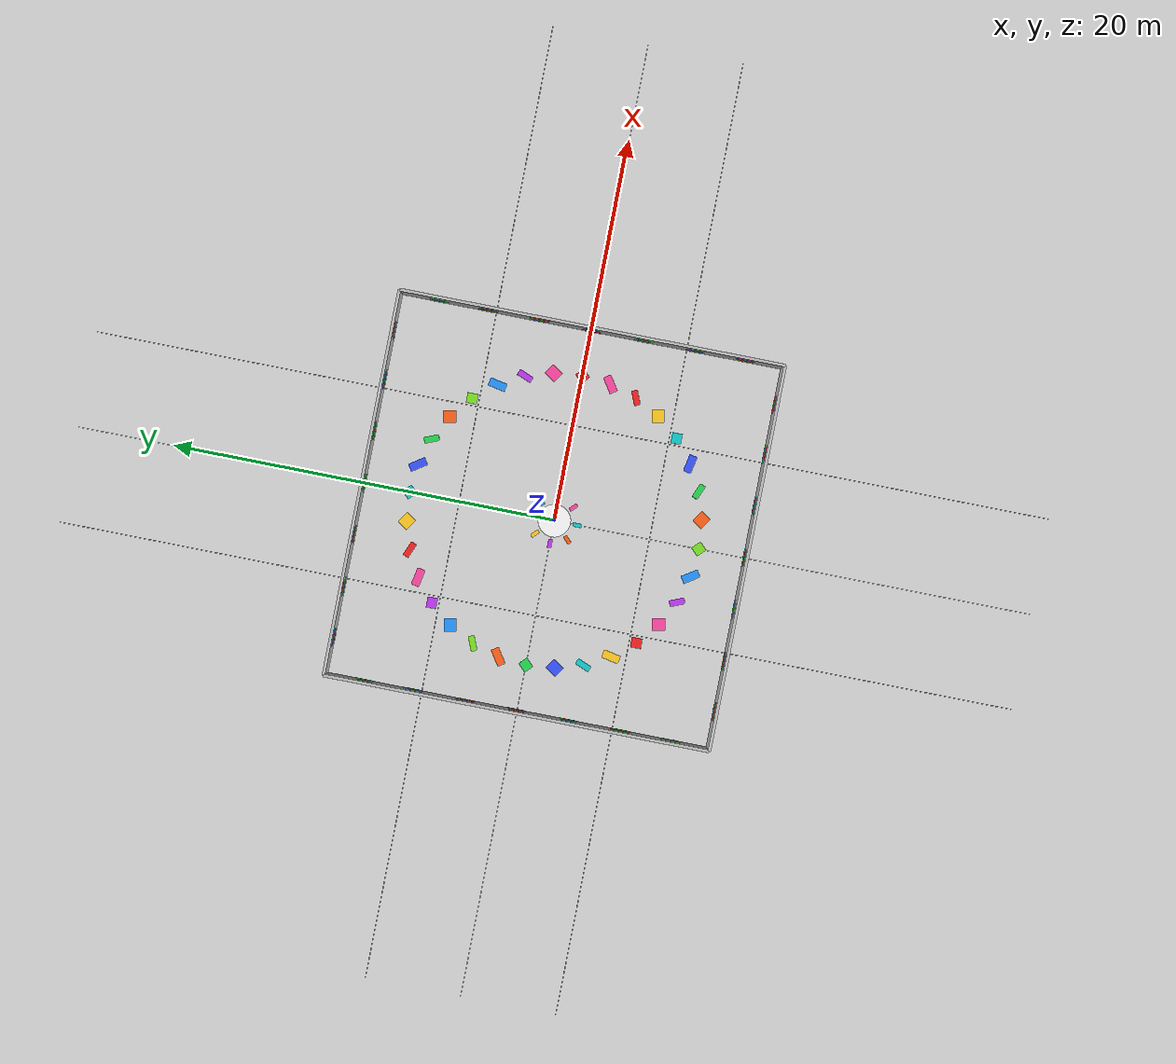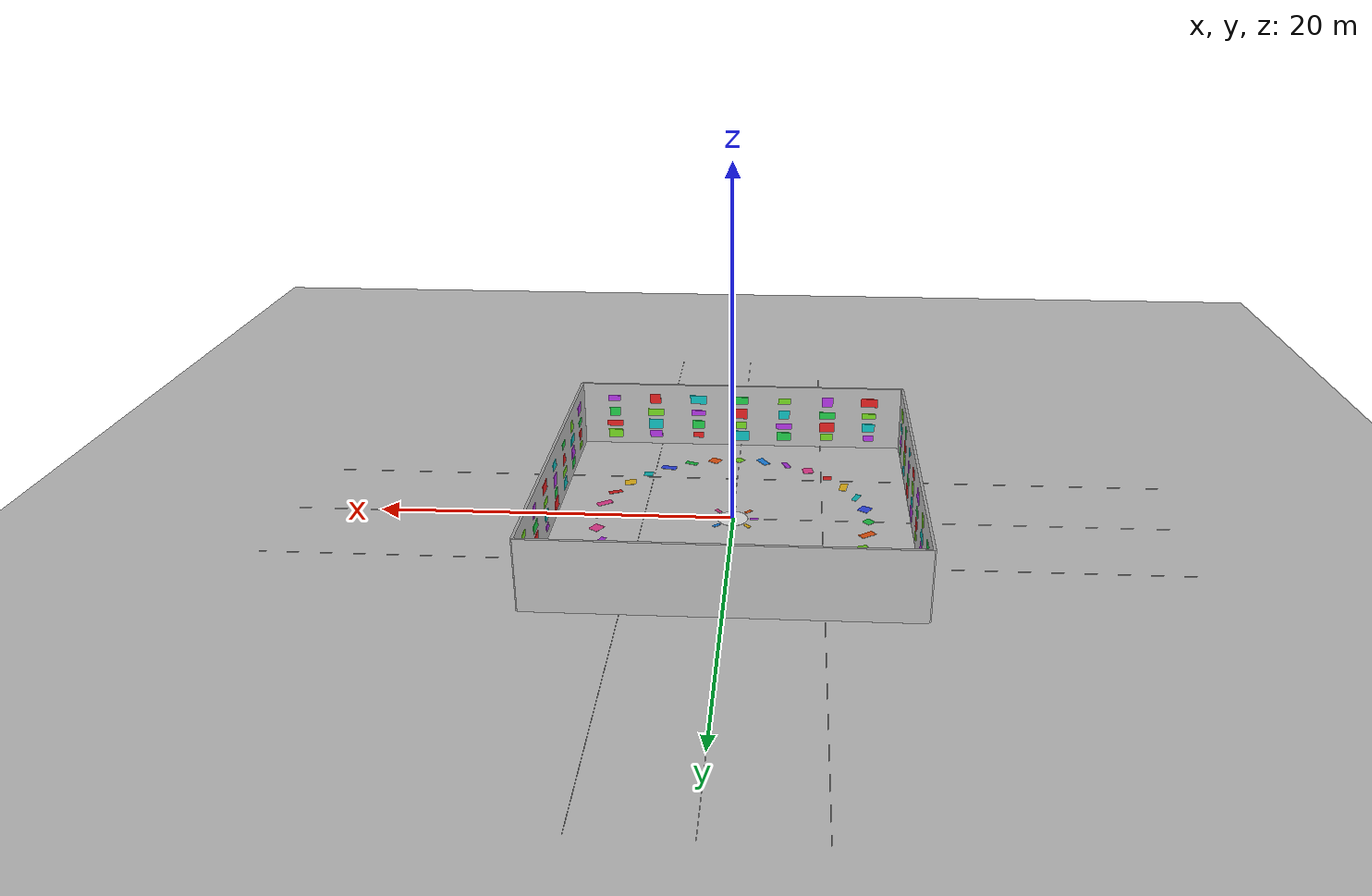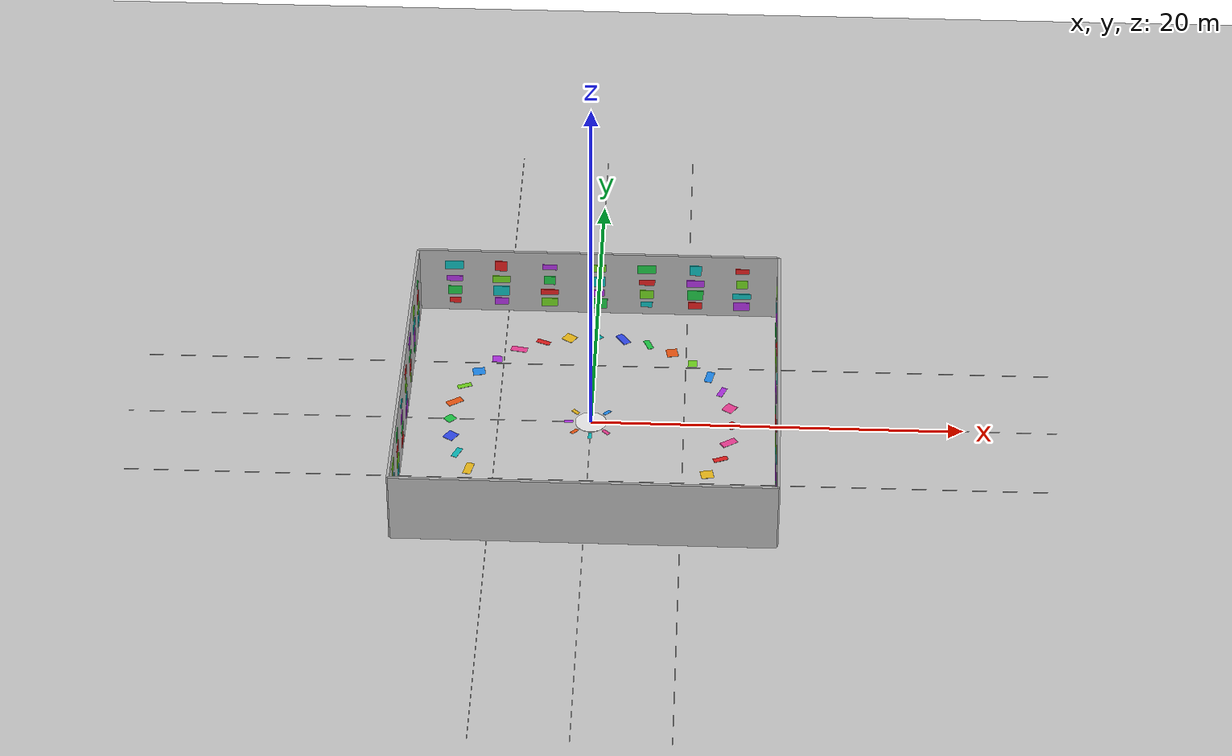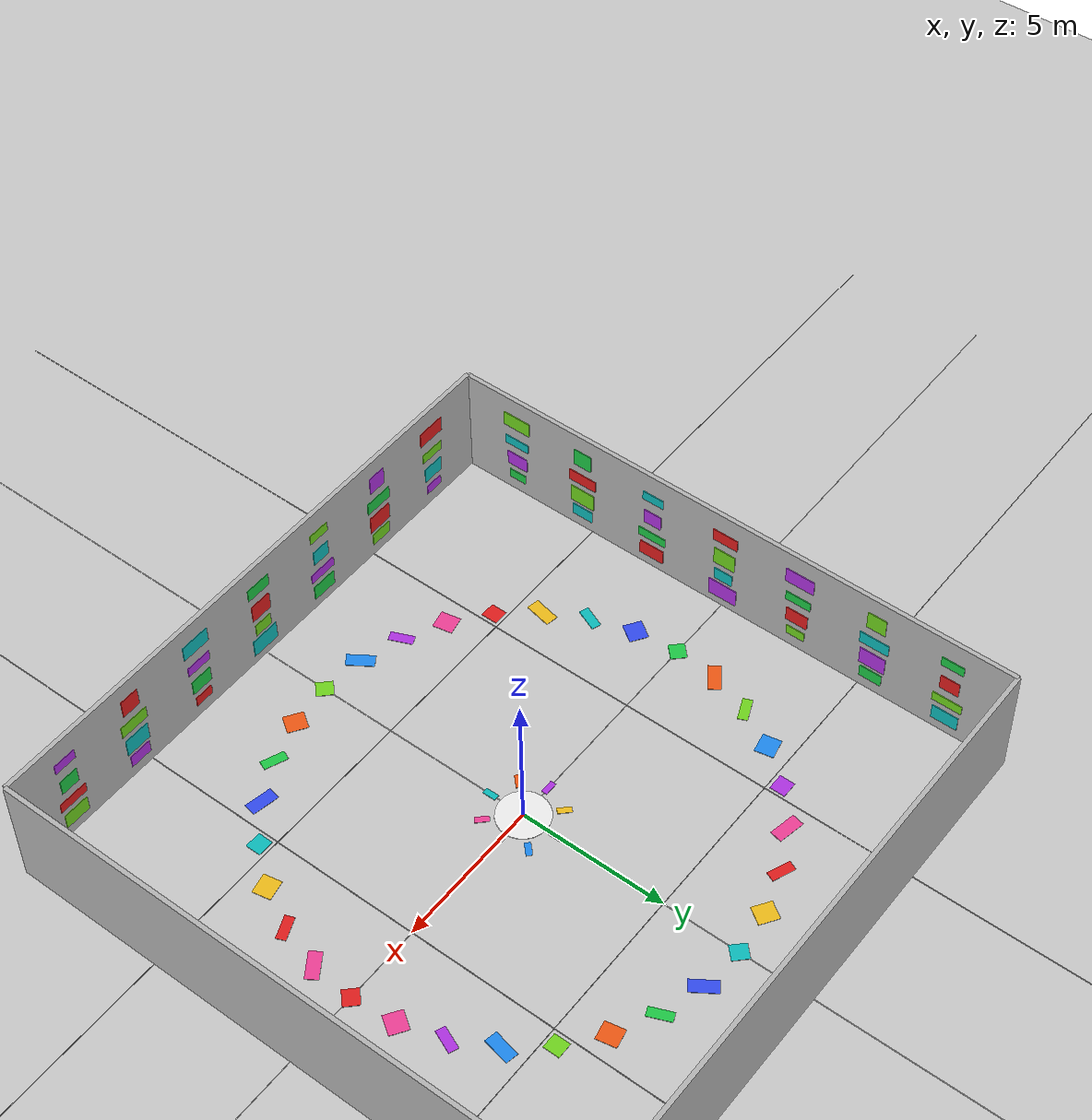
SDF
<?xml version='1.0' encoding='utf-8'?>
<sdf version="1.9">
  <world name="vio_marker_arena">
    <physics type="ode">
      <max_step_size>0.004</max_step_size>
      <real_time_factor>1.0</real_time_factor>
      <real_time_update_rate>250</real_time_update_rate>
    </physics>
    <gravity>0 0 -9.8</gravity>
    <magnetic_field>6e-06 2.3e-05 -4.2e-05</magnetic_field>
    <atmosphere type="adiabatic" />
    <scene>
      <grid>false</grid>
      <ambient>0.65 0.65 0.65 1</ambient>
      <background>0.72 0.78 0.86 1</background>
      <shadows>true</shadows>
    </scene>
    <model name="ground_plane">
      <static>true</static>
      <link name="link">
        <collision name="collision">
          <geometry>
            <plane>
              <normal>0 0 1</normal>
              <size>1 1</size>
            </plane>
          </geometry>
          <surface>
            <friction>
              <ode />
            </friction>
            <bounce />
            <contact />
          </surface>
        </collision>
        <visual name="visual">
          <geometry>
            <plane>
              <normal>0 0 1</normal>
              <size>500 500</size>
            </plane>
          </geometry>
          <material>
            <ambient>0.8 0.8 0.8 1</ambient>
            <diffuse>0.8 0.8 0.8 1</diffuse>
            <specular>0.8 0.8 0.8 1</specular>
          </material>
        </visual>
        <pose>0 0 0 0 -0 0</pose>
        <inertial>
          <pose>0 0 0 0 -0 0</pose>
          <mass>1</mass>
          <inertia>
            <ixx>1</ixx>
            <ixy>0</ixy>
            <ixz>0</ixz>
            <iyy>1</iyy>
            <iyz>0</iyz>
            <izz>1</izz>
          </inertia>
        </inertial>
        <enable_wind>false</enable_wind>
      </link>
      <pose>0 0 0 0 -0 0</pose>
      <self_collide>false</self_collide>
    </model>
    <light name="sunUTC" type="directional">
      <pose>0 0 500 0 -0 0</pose>
      <cast_shadows>true</cast_shadows>
      <intensity>1</intensity>
      <direction>0.001 0.625 -0.78</direction>
      <diffuse>0.904 0.904 0.904 1</diffuse>
      <specular>0.271 0.271 0.271 1</specular>
      <attenuation>
        <range>2000</range>
        <linear>0</linear>
        <constant>1</constant>
        <quadratic>0</quadratic>
      </attenuation>
      <spot>
        <inner_angle>0</inner_angle>
        <outer_angle>0</outer_angle>
        <falloff>0</falloff>
      </spot>
    </light>
    <spherical_coordinates>
      <surface_model>EARTH_WGS84</surface_model>
      <world_frame_orientation>ENU</world_frame_orientation>
      <latitude_deg>47.397971057728974</latitude_deg>
      <longitude_deg> 8.546163739800146</longitude_deg>
      <elevation>0</elevation>
    </spherical_coordinates>
    <model name="visual_grid">
      <static>true</static>
      <pose>0 0 0.01 0 0 0</pose>
      <link name="grid_link">
        <visual name="x_line_1">
          <pose>0 0 0 0 0 0</pose>
          <geometry>
            <box>
              <size>50 0.02 0.01</size>
            </box>
          </geometry>
          <material>
            <ambient>0.7 0.7 0.7 1</ambient>
            <diffuse>0.7 0.7 0.7 1</diffuse>
          </material>
        </visual>
        <visual name="y_line_1">
          <pose>0 0 0 0 0 1.5708</pose>
          <geometry>
            <box>
              <size>50 0.02 0.01</size>
            </box>
          </geometry>
          <material>
            <ambient>0.7 0.7 0.7 1</ambient>
            <diffuse>0.7 0.7 0.7 1</diffuse>
          </material>
        </visual>
        <visual name="x_line_5">
          <pose>0 5 0 0 0 0</pose>
          <geometry>
            <box>
              <size>50 0.02 0.01</size>
            </box>
          </geometry>
          <material>
            <ambient>0.5 0.5 0.5 1</ambient>
            <diffuse>0.5 0.5 0.5 1</diffuse>
          </material>
        </visual>
        <visual name="x_line_minus5">
          <pose>0 -5 0 0 0 0</pose>
          <geometry>
            <box>
              <size>50 0.02 0.01</size>
            </box>
          </geometry>
          <material>
            <ambient>0.5 0.5 0.5 1</ambient>
            <diffuse>0.5 0.5 0.5 1</diffuse>
          </material>
        </visual>
        <visual name="y_line_5">
          <pose>5 0 0 0 0 1.5708</pose>
          <geometry>
            <box>
              <size>50 0.02 0.01</size>
            </box>
          </geometry>
          <material>
            <ambient>0.5 0.5 0.5 1</ambient>
            <diffuse>0.5 0.5 0.5 1</diffuse>
          </material>
        </visual>
        <visual name="y_line_minus5">
          <pose>-5 0 0 0 0 1.5708</pose>
          <geometry>
            <box>
              <size>50 0.02 0.01</size>
            </box>
          </geometry>
          <material>
            <ambient>0.5 0.5 0.5 1</ambient>
            <diffuse>0.5 0.5 0.5 1</diffuse>
          </material>
        </visual>
      </link>
    </model>
    <model name="vio_wall_north">
      <static>true</static>
      <pose>0.0000 10.0000 2.0000 0.0000 0.0000 0.0000</pose>
      <link name="link">
        <collision name="collision">
          <geometry>
            <box>
              <size>20.0000 0.1500 4.0000</size>
            </box>
          </geometry>
        </collision>
        <visual name="visual">
          <geometry>
            <box>
              <size>20.0000 0.1500 4.0000</size>
            </box>
          </geometry>
          <material>
            <ambient>0.720 0.720 0.720 1.000</ambient>
            <diffuse>0.720 0.720 0.720 1.000</diffuse>
            <specular>0.10 0.10 0.10 1</specular>
            <emissive>0 0 0 1</emissive>
          </material>
        </visual>
      </link>
    </model>
    <model name="vio_wall_south">
      <static>true</static>
      <pose>0.0000 -10.0000 2.0000 0.0000 0.0000 0.0000</pose>
      <link name="link">
        <collision name="collision">
          <geometry>
            <box>
              <size>20.0000 0.1500 4.0000</size>
            </box>
          </geometry>
        </collision>
        <visual name="visual">
          <geometry>
            <box>
              <size>20.0000 0.1500 4.0000</size>
            </box>
          </geometry>
          <material>
            <ambient>0.720 0.720 0.720 1.000</ambient>
            <diffuse>0.720 0.720 0.720 1.000</diffuse>
            <specular>0.10 0.10 0.10 1</specular>
            <emissive>0 0 0 1</emissive>
          </material>
        </visual>
      </link>
    </model>
    <model name="vio_wall_east">
      <static>true</static>
      <pose>10.0000 0.0000 2.0000 0.0000 0.0000 0.0000</pose>
      <link name="link">
        <collision name="collision">
          <geometry>
            <box>
              <size>0.1500 20.0000 4.0000</size>
            </box>
          </geometry>
        </collision>
        <visual name="visual">
          <geometry>
            <box>
              <size>0.1500 20.0000 4.0000</size>
            </box>
          </geometry>
          <material>
            <ambient>0.720 0.720 0.720 1.000</ambient>
            <diffuse>0.720 0.720 0.720 1.000</diffuse>
            <specular>0.10 0.10 0.10 1</specular>
            <emissive>0 0 0 1</emissive>
          </material>
        </visual>
      </link>
    </model>
    <model name="vio_wall_west">
      <static>true</static>
      <pose>-10.0000 0.0000 2.0000 0.0000 0.0000 0.0000</pose>
      <link name="link">
        <collision name="collision">
          <geometry>
            <box>
              <size>0.1500 20.0000 4.0000</size>
            </box>
          </geometry>
        </collision>
        <visual name="visual">
          <geometry>
            <box>
              <size>0.1500 20.0000 4.0000</size>
            </box>
          </geometry>
          <material>
            <ambient>0.720 0.720 0.720 1.000</ambient>
            <diffuse>0.720 0.720 0.720 1.000</diffuse>
            <specular>0.10 0.10 0.10 1</specular>
            <emissive>0 0 0 1</emissive>
          </material>
        </visual>
      </link>
    </model>
    <model name="vio_panel_north_0_0">
      <static>true</static>
      <pose>-8.0000 9.9190 0.6500 0.0000 0.0000 0.0000</pose>
      <link name="link">
        <visual name="visual">
          <geometry>
            <box>
              <size>0.6500 0.0350 0.3500</size>
            </box>
          </geometry>
          <material>
            <ambient>0.900 0.120 0.120 1.000</ambient>
            <diffuse>0.900 0.120 0.120 1.000</diffuse>
            <specular>0.10 0.10 0.10 1</specular>
            <emissive>0 0 0 1</emissive>
          </material>
        </visual>
      </link>
    </model>
    <model name="vio_panel_north_0_1">
      <static>true</static>
      <pose>-5.4000 9.9190 0.6500 0.0000 0.0000 0.0000</pose>
      <link name="link">
        <visual name="visual">
          <geometry>
            <box>
              <size>0.7700 0.0350 0.4500</size>
            </box>
          </geometry>
          <material>
            <ambient>0.700 0.200 0.900 1.000</ambient>
            <diffuse>0.700 0.200 0.900 1.000</diffuse>
            <specular>0.10 0.10 0.10 1</specular>
            <emissive>0 0 0 1</emissive>
          </material>
        </visual>
      </link>
    </model>
    <model name="vio_panel_north_0_2">
      <static>true</static>
      <pose>-2.7000 9.9190 0.6500 0.0000 0.0000 0.0000</pose>
      <link name="link">
        <visual name="visual">
          <geometry>
            <box>
              <size>0.8900 0.0350 0.5500</size>
            </box>
          </geometry>
          <material>
            <ambient>0.450 0.850 0.120 1.000</ambient>
            <diffuse>0.450 0.850 0.120 1.000</diffuse>
            <specular>0.10 0.10 0.10 1</specular>
            <emissive>0 0 0 1</emissive>
          </material>
        </visual>
      </link>
    </model>
    <model name="vio_panel_north_0_3">
      <static>true</static>
      <pose>0.0000 9.9190 0.6500 0.0000 0.0000 0.0000</pose>
      <link name="link">
        <visual name="visual">
          <geometry>
            <box>
              <size>1.0100 0.0350 0.6500</size>
            </box>
          </geometry>
          <material>
            <ambient>0.120 0.800 0.280 1.000</ambient>
            <diffuse>0.120 0.800 0.280 1.000</diffuse>
            <specular>0.10 0.10 0.10 1</specular>
            <emissive>0 0 0 1</emissive>
          </material>
        </visual>
      </link>
    </model>
    <model name="vio_panel_north_0_4">
      <static>true</static>
      <pose>2.7000 9.9190 0.6500 0.0000 0.0000 0.0000</pose>
      <link name="link">
        <visual name="visual">
          <geometry>
            <box>
              <size>0.6500 0.0350 0.3500</size>
            </box>
          </geometry>
          <material>
            <ambient>0.050 0.750 0.750 1.000</ambient>
            <diffuse>0.050 0.750 0.750 1.000</diffuse>
            <specular>0.10 0.10 0.10 1</specular>
            <emissive>0 0 0 1</emissive>
          </material>
        </visual>
      </link>
    </model>
    <model name="vio_panel_north_0_5">
      <static>true</static>
      <pose>5.4000 9.9190 0.6500 0.0000 0.0000 0.0000</pose>
      <link name="link">
        <visual name="visual">
          <geometry>
            <box>
              <size>0.7700 0.0350 0.4500</size>
            </box>
          </geometry>
          <material>
            <ambient>0.900 0.120 0.120 1.000</ambient>
            <diffuse>0.900 0.120 0.120 1.000</diffuse>
            <specular>0.10 0.10 0.10 1</specular>
            <emissive>0 0 0 1</emissive>
          </material>
        </visual>
      </link>
    </model>
    <model name="vio_panel_north_0_6">
      <static>true</static>
      <pose>8.0000 9.9190 0.6500 0.0000 0.0000 0.0000</pose>
      <link name="link">
        <visual name="visual">
          <geometry>
            <box>
              <size>0.8900 0.0350 0.5500</size>
            </box>
          </geometry>
          <material>
            <ambient>0.700 0.200 0.900 1.000</ambient>
            <diffuse>0.700 0.200 0.900 1.000</diffuse>
            <specular>0.10 0.10 0.10 1</specular>
            <emissive>0 0 0 1</emissive>
          </material>
        </visual>
      </link>
    </model>
    <model name="vio_panel_north_1_0">
      <static>true</static>
      <pose>-8.0000 9.9190 1.3500 0.0000 0.0000 0.0000</pose>
      <link name="link">
        <visual name="visual">
          <geometry>
            <box>
              <size>0.7700 0.0350 0.5500</size>
            </box>
          </geometry>
          <material>
            <ambient>0.120 0.800 0.280 1.000</ambient>
            <diffuse>0.120 0.800 0.280 1.000</diffuse>
            <specular>0.10 0.10 0.10 1</specular>
            <emissive>0 0 0 1</emissive>
          </material>
        </visual>
      </link>
    </model>
    <model name="vio_panel_north_1_1">
      <static>true</static>
      <pose>-5.4000 9.9190 1.3500 0.0000 0.0000 0.0000</pose>
      <link name="link">
        <visual name="visual">
          <geometry>
            <box>
              <size>0.8900 0.0350 0.6500</size>
            </box>
          </geometry>
          <material>
            <ambient>0.050 0.750 0.750 1.000</ambient>
            <diffuse>0.050 0.750 0.750 1.000</diffuse>
            <specular>0.10 0.10 0.10 1</specular>
            <emissive>0 0 0 1</emissive>
          </material>
        </visual>
      </link>
    </model>
    <model name="vio_panel_north_1_2">
      <static>true</static>
      <pose>-2.7000 9.9190 1.3500 0.0000 0.0000 0.0000</pose>
      <link name="link">
        <visual name="visual">
          <geometry>
            <box>
              <size>1.0100 0.0350 0.3500</size>
            </box>
          </geometry>
          <material>
            <ambient>0.900 0.120 0.120 1.000</ambient>
            <diffuse>0.900 0.120 0.120 1.000</diffuse>
            <specular>0.10 0.10 0.10 1</specular>
            <emissive>0 0 0 1</emissive>
          </material>
        </visual>
      </link>
    </model>
    <model name="vio_panel_north_1_3">
      <static>true</static>
      <pose>0.0000 9.9190 1.3500 0.0000 0.0000 0.0000</pose>
      <link name="link">
        <visual name="visual">
          <geometry>
            <box>
              <size>0.6500 0.0350 0.4500</size>
            </box>
          </geometry>
          <material>
            <ambient>0.700 0.200 0.900 1.000</ambient>
            <diffuse>0.700 0.200 0.900 1.000</diffuse>
            <specular>0.10 0.10 0.10 1</specular>
            <emissive>0 0 0 1</emissive>
          </material>
        </visual>
      </link>
    </model>
    <model name="vio_panel_north_1_4">
      <static>true</static>
      <pose>2.7000 9.9190 1.3500 0.0000 0.0000 0.0000</pose>
      <link name="link">
        <visual name="visual">
          <geometry>
            <box>
              <size>0.7700 0.0350 0.5500</size>
            </box>
          </geometry>
          <material>
            <ambient>0.450 0.850 0.120 1.000</ambient>
            <diffuse>0.450 0.850 0.120 1.000</diffuse>
            <specular>0.10 0.10 0.10 1</specular>
            <emissive>0 0 0 1</emissive>
          </material>
        </visual>
      </link>
    </model>
    <model name="vio_panel_north_1_5">
      <static>true</static>
      <pose>5.4000 9.9190 1.3500 0.0000 0.0000 0.0000</pose>
      <link name="link">
        <visual name="visual">
          <geometry>
            <box>
              <size>0.8900 0.0350 0.6500</size>
            </box>
          </geometry>
          <material>
            <ambient>0.120 0.800 0.280 1.000</ambient>
            <diffuse>0.120 0.800 0.280 1.000</diffuse>
            <specular>0.10 0.10 0.10 1</specular>
            <emissive>0 0 0 1</emissive>
          </material>
        </visual>
      </link>
    </model>
    <model name="vio_panel_north_1_6">
      <static>true</static>
      <pose>8.0000 9.9190 1.3500 0.0000 0.0000 0.0000</pose>
      <link name="link">
        <visual name="visual">
          <geometry>
            <box>
              <size>1.0100 0.0350 0.3500</size>
            </box>
          </geometry>
          <material>
            <ambient>0.050 0.750 0.750 1.000</ambient>
            <diffuse>0.050 0.750 0.750 1.000</diffuse>
            <specular>0.10 0.10 0.10 1</specular>
            <emissive>0 0 0 1</emissive>
          </material>
        </visual>
      </link>
    </model>
    <model name="vio_panel_north_2_0">
      <static>true</static>
      <pose>-8.0000 9.9190 2.1500 0.0000 0.0000 0.0000</pose>
      <link name="link">
        <visual name="visual">
          <geometry>
            <box>
              <size>0.8900 0.0350 0.3500</size>
            </box>
          </geometry>
          <material>
            <ambient>0.700 0.200 0.900 1.000</ambient>
            <diffuse>0.700 0.200 0.900 1.000</diffuse>
            <specular>0.10 0.10 0.10 1</specular>
            <emissive>0 0 0 1</emissive>
          </material>
        </visual>
      </link>
    </model>
    <model name="vio_panel_north_2_1">
      <static>true</static>
      <pose>-5.4000 9.9190 2.1500 0.0000 0.0000 0.0000</pose>
      <link name="link">
        <visual name="visual">
          <geometry>
            <box>
              <size>1.0100 0.0350 0.4500</size>
            </box>
          </geometry>
          <material>
            <ambient>0.450 0.850 0.120 1.000</ambient>
            <diffuse>0.450 0.850 0.120 1.000</diffuse>
            <specular>0.10 0.10 0.10 1</specular>
            <emissive>0 0 0 1</emissive>
          </material>
        </visual>
      </link>
    </model>
    <model name="vio_panel_north_2_2">
      <static>true</static>
      <pose>-2.7000 9.9190 2.1500 0.0000 0.0000 0.0000</pose>
      <link name="link">
        <visual name="visual">
          <geometry>
            <box>
              <size>0.6500 0.0350 0.5500</size>
            </box>
          </geometry>
          <material>
            <ambient>0.120 0.800 0.280 1.000</ambient>
            <diffuse>0.120 0.800 0.280 1.000</diffuse>
            <specular>0.10 0.10 0.10 1</specular>
            <emissive>0 0 0 1</emissive>
          </material>
        </visual>
      </link>
    </model>
    <model name="vio_panel_north_2_3">
      <static>true</static>
      <pose>0.0000 9.9190 2.1500 0.0000 0.0000 0.0000</pose>
      <link name="link">
        <visual name="visual">
          <geometry>
            <box>
              <size>0.7700 0.0350 0.6500</size>
            </box>
          </geometry>
          <material>
            <ambient>0.050 0.750 0.750 1.000</ambient>
            <diffuse>0.050 0.750 0.750 1.000</diffuse>
            <specular>0.10 0.10 0.10 1</specular>
            <emissive>0 0 0 1</emissive>
          </material>
        </visual>
      </link>
    </model>
    <model name="vio_panel_north_2_4">
      <static>true</static>
      <pose>2.7000 9.9190 2.1500 0.0000 0.0000 0.0000</pose>
      <link name="link">
        <visual name="visual">
          <geometry>
            <box>
              <size>0.8900 0.0350 0.3500</size>
            </box>
          </geometry>
          <material>
            <ambient>0.900 0.120 0.120 1.000</ambient>
            <diffuse>0.900 0.120 0.120 1.000</diffuse>
            <specular>0.10 0.10 0.10 1</specular>
            <emissive>0 0 0 1</emissive>
          </material>
        </visual>
      </link>
    </model>
    <model name="vio_panel_north_2_5">
      <static>true</static>
      <pose>5.4000 9.9190 2.1500 0.0000 0.0000 0.0000</pose>
      <link name="link">
        <visual name="visual">
          <geometry>
            <box>
              <size>1.0100 0.0350 0.4500</size>
            </box>
          </geometry>
          <material>
            <ambient>0.700 0.200 0.900 1.000</ambient>
            <diffuse>0.700 0.200 0.900 1.000</diffuse>
            <specular>0.10 0.10 0.10 1</specular>
            <emissive>0 0 0 1</emissive>
          </material>
        </visual>
      </link>
    </model>
    <model name="vio_panel_north_2_6">
      <static>true</static>
      <pose>8.0000 9.9190 2.1500 0.0000 0.0000 0.0000</pose>
      <link name="link">
        <visual name="visual">
          <geometry>
            <box>
              <size>0.6500 0.0350 0.5500</size>
            </box>
          </geometry>
          <material>
            <ambient>0.450 0.850 0.120 1.000</ambient>
            <diffuse>0.450 0.850 0.120 1.000</diffuse>
            <specular>0.10 0.10 0.10 1</specular>
            <emissive>0 0 0 1</emissive>
          </material>
        </visual>
      </link>
    </model>
    <model name="vio_panel_north_3_0">
      <static>true</static>
      <pose>-8.0000 9.9190 3.0500 0.0000 0.0000 0.0000</pose>
      <link name="link">
        <visual name="visual">
          <geometry>
            <box>
              <size>1.0100 0.0350 0.5500</size>
            </box>
          </geometry>
          <material>
            <ambient>0.050 0.750 0.750 1.000</ambient>
            <diffuse>0.050 0.750 0.750 1.000</diffuse>
            <specular>0.10 0.10 0.10 1</specular>
            <emissive>0 0 0 1</emissive>
          </material>
        </visual>
      </link>
    </model>
    <model name="vio_panel_north_3_1">
      <static>true</static>
      <pose>-5.4000 9.9190 3.0500 0.0000 0.0000 0.0000</pose>
      <link name="link">
        <visual name="visual">
          <geometry>
            <box>
              <size>0.6500 0.0350 0.6500</size>
            </box>
          </geometry>
          <material>
            <ambient>0.900 0.120 0.120 1.000</ambient>
            <diffuse>0.900 0.120 0.120 1.000</diffuse>
            <specular>0.10 0.10 0.10 1</specular>
            <emissive>0 0 0 1</emissive>
          </material>
        </visual>
      </link>
    </model>
    <model name="vio_panel_north_3_2">
      <static>true</static>
      <pose>-2.7000 9.9190 3.0500 0.0000 0.0000 0.0000</pose>
      <link name="link">
        <visual name="visual">
          <geometry>
            <box>
              <size>0.7700 0.0350 0.3500</size>
            </box>
          </geometry>
          <material>
            <ambient>0.700 0.200 0.900 1.000</ambient>
            <diffuse>0.700 0.200 0.900 1.000</diffuse>
            <specular>0.10 0.10 0.10 1</specular>
            <emissive>0 0 0 1</emissive>
          </material>
        </visual>
      </link>
    </model>
    <model name="vio_panel_north_3_3">
      <static>true</static>
      <pose>0.0000 9.9190 3.0500 0.0000 0.0000 0.0000</pose>
      <link name="link">
        <visual name="visual">
          <geometry>
            <box>
              <size>0.8900 0.0350 0.4500</size>
            </box>
          </geometry>
          <material>
            <ambient>0.450 0.850 0.120 1.000</ambient>
            <diffuse>0.450 0.850 0.120 1.000</diffuse>
            <specular>0.10 0.10 0.10 1</specular>
            <emissive>0 0 0 1</emissive>
          </material>
        </visual>
      </link>
    </model>
    <model name="vio_panel_north_3_4">
      <static>true</static>
      <pose>2.7000 9.9190 3.0500 0.0000 0.0000 0.0000</pose>
      <link name="link">
        <visual name="visual">
          <geometry>
            <box>
              <size>1.0100 0.0350 0.5500</size>
            </box>
          </geometry>
          <material>
            <ambient>0.120 0.800 0.280 1.000</ambient>
            <diffuse>0.120 0.800 0.280 1.000</diffuse>
            <specular>0.10 0.10 0.10 1</specular>
            <emissive>0 0 0 1</emissive>
          </material>
        </visual>
      </link>
    </model>
    <model name="vio_panel_north_3_5">
      <static>true</static>
      <pose>5.4000 9.9190 3.0500 0.0000 0.0000 0.0000</pose>
      <link name="link">
        <visual name="visual">
          <geometry>
            <box>
              <size>0.6500 0.0350 0.6500</size>
            </box>
          </geometry>
          <material>
            <ambient>0.050 0.750 0.750 1.000</ambient>
            <diffuse>0.050 0.750 0.750 1.000</diffuse>
            <specular>0.10 0.10 0.10 1</specular>
            <emissive>0 0 0 1</emissive>
          </material>
        </visual>
      </link>
    </model>
    <model name="vio_panel_north_3_6">
      <static>true</static>
      <pose>8.0000 9.9190 3.0500 0.0000 0.0000 0.0000</pose>
      <link name="link">
        <visual name="visual">
          <geometry>
            <box>
              <size>0.7700 0.0350 0.3500</size>
            </box>
          </geometry>
          <material>
            <ambient>0.900 0.120 0.120 1.000</ambient>
            <diffuse>0.900 0.120 0.120 1.000</diffuse>
            <specular>0.10 0.10 0.10 1</specular>
            <emissive>0 0 0 1</emissive>
          </material>
        </visual>
      </link>
    </model>
    <model name="vio_panel_south_0_0">
      <static>true</static>
      <pose>-8.0000 -9.9190 0.6500 0.0000 0.0000 0.0000</pose>
      <link name="link">
        <visual name="visual">
          <geometry>
            <box>
              <size>0.6500 0.0350 0.3500</size>
            </box>
          </geometry>
          <material>
            <ambient>0.700 0.200 0.900 1.000</ambient>
            <diffuse>0.700 0.200 0.900 1.000</diffuse>
            <specular>0.10 0.10 0.10 1</specular>
            <emissive>0 0 0 1</emissive>
          </material>
        </visual>
      </link>
    </model>
    <model name="vio_panel_south_0_1">
      <static>true</static>
      <pose>-5.4000 -9.9190 0.6500 0.0000 0.0000 0.0000</pose>
      <link name="link">
        <visual name="visual">
          <geometry>
            <box>
              <size>0.7700 0.0350 0.4500</size>
            </box>
          </geometry>
          <material>
            <ambient>0.450 0.850 0.120 1.000</ambient>
            <diffuse>0.450 0.850 0.120 1.000</diffuse>
            <specular>0.10 0.10 0.10 1</specular>
            <emissive>0 0 0 1</emissive>
          </material>
        </visual>
      </link>
    </model>
    <model name="vio_panel_south_0_2">
      <static>true</static>
      <pose>-2.7000 -9.9190 0.6500 0.0000 0.0000 0.0000</pose>
      <link name="link">
        <visual name="visual">
          <geometry>
            <box>
              <size>0.8900 0.0350 0.5500</size>
            </box>
          </geometry>
          <material>
            <ambient>0.120 0.800 0.280 1.000</ambient>
            <diffuse>0.120 0.800 0.280 1.000</diffuse>
            <specular>0.10 0.10 0.10 1</specular>
            <emissive>0 0 0 1</emissive>
          </material>
        </visual>
      </link>
    </model>
    <model name="vio_panel_south_0_3">
      <static>true</static>
      <pose>0.0000 -9.9190 0.6500 0.0000 0.0000 0.0000</pose>
      <link name="link">
        <visual name="visual">
          <geometry>
            <box>
              <size>1.0100 0.0350 0.6500</size>
            </box>
          </geometry>
          <material>
            <ambient>0.050 0.750 0.750 1.000</ambient>
            <diffuse>0.050 0.750 0.750 1.000</diffuse>
            <specular>0.10 0.10 0.10 1</specular>
            <emissive>0 0 0 1</emissive>
          </material>
        </visual>
      </link>
    </model>
    <model name="vio_panel_south_0_4">
      <static>true</static>
      <pose>2.7000 -9.9190 0.6500 0.0000 0.0000 0.0000</pose>
      <link name="link">
        <visual name="visual">
          <geometry>
            <box>
              <size>0.6500 0.0350 0.3500</size>
            </box>
          </geometry>
          <material>
            <ambient>0.900 0.120 0.120 1.000</ambient>
            <diffuse>0.900 0.120 0.120 1.000</diffuse>
            <specular>0.10 0.10 0.10 1</specular>
            <emissive>0 0 0 1</emissive>
          </material>
        </visual>
      </link>
    </model>
    <model name="vio_panel_south_0_5">
      <static>true</static>
      <pose>5.4000 -9.9190 0.6500 0.0000 0.0000 0.0000</pose>
      <link name="link">
        <visual name="visual">
          <geometry>
            <box>
              <size>0.7700 0.0350 0.4500</size>
            </box>
          </geometry>
          <material>
            <ambient>0.700 0.200 0.900 1.000</ambient>
            <diffuse>0.700 0.200 0.900 1.000</diffuse>
            <specular>0.10 0.10 0.10 1</specular>
            <emissive>0 0 0 1</emissive>
          </material>
        </visual>
      </link>
    </model>
    <model name="vio_panel_south_0_6">
      <static>true</static>
      <pose>8.0000 -9.9190 0.6500 0.0000 0.0000 0.0000</pose>
      <link name="link">
        <visual name="visual">
          <geometry>
            <box>
              <size>0.8900 0.0350 0.5500</size>
            </box>
          </geometry>
          <material>
            <ambient>0.450 0.850 0.120 1.000</ambient>
            <diffuse>0.450 0.850 0.120 1.000</diffuse>
            <specular>0.10 0.10 0.10 1</specular>
            <emissive>0 0 0 1</emissive>
          </material>
        </visual>
      </link>
    </model>
    <model name="vio_panel_south_1_0">
      <static>true</static>
      <pose>-8.0000 -9.9190 1.3500 0.0000 0.0000 0.0000</pose>
      <link name="link">
        <visual name="visual">
          <geometry>
            <box>
              <size>0.7700 0.0350 0.5500</size>
            </box>
          </geometry>
          <material>
            <ambient>0.050 0.750 0.750 1.000</ambient>
            <diffuse>0.050 0.750 0.750 1.000</diffuse>
            <specular>0.10 0.10 0.10 1</specular>
            <emissive>0 0 0 1</emissive>
          </material>
        </visual>
      </link>
    </model>
    <model name="vio_panel_south_1_1">
      <static>true</static>
      <pose>-5.4000 -9.9190 1.3500 0.0000 0.0000 0.0000</pose>
      <link name="link">
        <visual name="visual">
          <geometry>
            <box>
              <size>0.8900 0.0350 0.6500</size>
            </box>
          </geometry>
          <material>
            <ambient>0.900 0.120 0.120 1.000</ambient>
            <diffuse>0.900 0.120 0.120 1.000</diffuse>
            <specular>0.10 0.10 0.10 1</specular>
            <emissive>0 0 0 1</emissive>
          </material>
        </visual>
      </link>
    </model>
    <model name="vio_panel_south_1_2">
      <static>true</static>
      <pose>-2.7000 -9.9190 1.3500 0.0000 0.0000 0.0000</pose>
      <link name="link">
        <visual name="visual">
          <geometry>
            <box>
              <size>1.0100 0.0350 0.3500</size>
            </box>
          </geometry>
          <material>
            <ambient>0.700 0.200 0.900 1.000</ambient>
            <diffuse>0.700 0.200 0.900 1.000</diffuse>
            <specular>0.10 0.10 0.10 1</specular>
            <emissive>0 0 0 1</emissive>
          </material>
        </visual>
      </link>
    </model>
    <model name="vio_panel_south_1_3">
      <static>true</static>
      <pose>0.0000 -9.9190 1.3500 0.0000 0.0000 0.0000</pose>
      <link name="link">
        <visual name="visual">
          <geometry>
            <box>
              <size>0.6500 0.0350 0.4500</size>
            </box>
          </geometry>
          <material>
            <ambient>0.450 0.850 0.120 1.000</ambient>
            <diffuse>0.450 0.850 0.120 1.000</diffuse>
            <specular>0.10 0.10 0.10 1</specular>
            <emissive>0 0 0 1</emissive>
          </material>
        </visual>
      </link>
    </model>
    <model name="vio_panel_south_1_4">
      <static>true</static>
      <pose>2.7000 -9.9190 1.3500 0.0000 0.0000 0.0000</pose>
      <link name="link">
        <visual name="visual">
          <geometry>
            <box>
              <size>0.7700 0.0350 0.5500</size>
            </box>
          </geometry>
          <material>
            <ambient>0.120 0.800 0.280 1.000</ambient>
            <diffuse>0.120 0.800 0.280 1.000</diffuse>
            <specular>0.10 0.10 0.10 1</specular>
            <emissive>0 0 0 1</emissive>
          </material>
        </visual>
      </link>
    </model>
    <model name="vio_panel_south_1_5">
      <static>true</static>
      <pose>5.4000 -9.9190 1.3500 0.0000 0.0000 0.0000</pose>
      <link name="link">
        <visual name="visual">
          <geometry>
            <box>
              <size>0.8900 0.0350 0.6500</size>
            </box>
          </geometry>
          <material>
            <ambient>0.050 0.750 0.750 1.000</ambient>
            <diffuse>0.050 0.750 0.750 1.000</diffuse>
            <specular>0.10 0.10 0.10 1</specular>
            <emissive>0 0 0 1</emissive>
          </material>
        </visual>
      </link>
    </model>
    <model name="vio_panel_south_1_6">
      <static>true</static>
      <pose>8.0000 -9.9190 1.3500 0.0000 0.0000 0.0000</pose>
      <link name="link">
        <visual name="visual">
          <geometry>
            <box>
              <size>1.0100 0.0350 0.3500</size>
            </box>
          </geometry>
          <material>
            <ambient>0.900 0.120 0.120 1.000</ambient>
            <diffuse>0.900 0.120 0.120 1.000</diffuse>
            <specular>0.10 0.10 0.10 1</specular>
            <emissive>0 0 0 1</emissive>
          </material>
        </visual>
      </link>
    </model>
    <model name="vio_panel_south_2_0">
      <static>true</static>
      <pose>-8.0000 -9.9190 2.1500 0.0000 0.0000 0.0000</pose>
      <link name="link">
        <visual name="visual">
          <geometry>
            <box>
              <size>0.8900 0.0350 0.3500</size>
            </box>
          </geometry>
          <material>
            <ambient>0.450 0.850 0.120 1.000</ambient>
            <diffuse>0.450 0.850 0.120 1.000</diffuse>
            <specular>0.10 0.10 0.10 1</specular>
            <emissive>0 0 0 1</emissive>
          </material>
        </visual>
      </link>
    </model>
    <model name="vio_panel_south_2_1">
      <static>true</static>
      <pose>-5.4000 -9.9190 2.1500 0.0000 0.0000 0.0000</pose>
      <link name="link">
        <visual name="visual">
          <geometry>
            <box>
              <size>1.0100 0.0350 0.4500</size>
            </box>
          </geometry>
          <material>
            <ambient>0.120 0.800 0.280 1.000</ambient>
            <diffuse>0.120 0.800 0.280 1.000</diffuse>
            <specular>0.10 0.10 0.10 1</specular>
            <emissive>0 0 0 1</emissive>
          </material>
        </visual>
      </link>
    </model>
    <model name="vio_panel_south_2_2">
      <static>true</static>
      <pose>-2.7000 -9.9190 2.1500 0.0000 0.0000 0.0000</pose>
      <link name="link">
        <visual name="visual">
          <geometry>
            <box>
              <size>0.6500 0.0350 0.5500</size>
            </box>
          </geometry>
          <material>
            <ambient>0.050 0.750 0.750 1.000</ambient>
            <diffuse>0.050 0.750 0.750 1.000</diffuse>
            <specular>0.10 0.10 0.10 1</specular>
            <emissive>0 0 0 1</emissive>
          </material>
        </visual>
      </link>
    </model>
    <model name="vio_panel_south_2_3">
      <static>true</static>
      <pose>0.0000 -9.9190 2.1500 0.0000 0.0000 0.0000</pose>
      <link name="link">
        <visual name="visual">
          <geometry>
            <box>
              <size>0.7700 0.0350 0.6500</size>
            </box>
          </geometry>
          <material>
            <ambient>0.900 0.120 0.120 1.000</ambient>
            <diffuse>0.900 0.120 0.120 1.000</diffuse>
            <specular>0.10 0.10 0.10 1</specular>
            <emissive>0 0 0 1</emissive>
          </material>
        </visual>
      </link>
    </model>
    <model name="vio_panel_south_2_4">
      <static>true</static>
      <pose>2.7000 -9.9190 2.1500 0.0000 0.0000 0.0000</pose>
      <link name="link">
        <visual name="visual">
          <geometry>
            <box>
              <size>0.8900 0.0350 0.3500</size>
            </box>
          </geometry>
          <material>
            <ambient>0.700 0.200 0.900 1.000</ambient>
            <diffuse>0.700 0.200 0.900 1.000</diffuse>
            <specular>0.10 0.10 0.10 1</specular>
            <emissive>0 0 0 1</emissive>
          </material>
        </visual>
      </link>
    </model>
    <model name="vio_panel_south_2_5">
      <static>true</static>
      <pose>5.4000 -9.9190 2.1500 0.0000 0.0000 0.0000</pose>
      <link name="link">
        <visual name="visual">
          <geometry>
            <box>
              <size>1.0100 0.0350 0.4500</size>
            </box>
          </geometry>
          <material>
            <ambient>0.450 0.850 0.120 1.000</ambient>
            <diffuse>0.450 0.850 0.120 1.000</diffuse>
            <specular>0.10 0.10 0.10 1</specular>
            <emissive>0 0 0 1</emissive>
          </material>
        </visual>
      </link>
    </model>
    <model name="vio_panel_south_2_6">
      <static>true</static>
      <pose>8.0000 -9.9190 2.1500 0.0000 0.0000 0.0000</pose>
      <link name="link">
        <visual name="visual">
          <geometry>
            <box>
              <size>0.6500 0.0350 0.5500</size>
            </box>
          </geometry>
          <material>
            <ambient>0.120 0.800 0.280 1.000</ambient>
            <diffuse>0.120 0.800 0.280 1.000</diffuse>
            <specular>0.10 0.10 0.10 1</specular>
            <emissive>0 0 0 1</emissive>
          </material>
        </visual>
      </link>
    </model>
    <model name="vio_panel_south_3_0">
      <static>true</static>
      <pose>-8.0000 -9.9190 3.0500 0.0000 0.0000 0.0000</pose>
      <link name="link">
        <visual name="visual">
          <geometry>
            <box>
              <size>1.0100 0.0350 0.5500</size>
            </box>
          </geometry>
          <material>
            <ambient>0.900 0.120 0.120 1.000</ambient>
            <diffuse>0.900 0.120 0.120 1.000</diffuse>
            <specular>0.10 0.10 0.10 1</specular>
            <emissive>0 0 0 1</emissive>
          </material>
        </visual>
      </link>
    </model>
    <model name="vio_panel_south_3_1">
      <static>true</static>
      <pose>-5.4000 -9.9190 3.0500 0.0000 0.0000 0.0000</pose>
      <link name="link">
        <visual name="visual">
          <geometry>
            <box>
              <size>0.6500 0.0350 0.6500</size>
            </box>
          </geometry>
          <material>
            <ambient>0.700 0.200 0.900 1.000</ambient>
            <diffuse>0.700 0.200 0.900 1.000</diffuse>
            <specular>0.10 0.10 0.10 1</specular>
            <emissive>0 0 0 1</emissive>
          </material>
        </visual>
      </link>
    </model>
    <model name="vio_panel_south_3_2">
      <static>true</static>
      <pose>-2.7000 -9.9190 3.0500 0.0000 0.0000 0.0000</pose>
      <link name="link">
        <visual name="visual">
          <geometry>
            <box>
              <size>0.7700 0.0350 0.3500</size>
            </box>
          </geometry>
          <material>
            <ambient>0.450 0.850 0.120 1.000</ambient>
            <diffuse>0.450 0.850 0.120 1.000</diffuse>
            <specular>0.10 0.10 0.10 1</specular>
            <emissive>0 0 0 1</emissive>
          </material>
        </visual>
      </link>
    </model>
    <model name="vio_panel_south_3_3">
      <static>true</static>
      <pose>0.0000 -9.9190 3.0500 0.0000 0.0000 0.0000</pose>
      <link name="link">
        <visual name="visual">
          <geometry>
            <box>
              <size>0.8900 0.0350 0.4500</size>
            </box>
          </geometry>
          <material>
            <ambient>0.120 0.800 0.280 1.000</ambient>
            <diffuse>0.120 0.800 0.280 1.000</diffuse>
            <specular>0.10 0.10 0.10 1</specular>
            <emissive>0 0 0 1</emissive>
          </material>
        </visual>
      </link>
    </model>
    <model name="vio_panel_south_3_4">
      <static>true</static>
      <pose>2.7000 -9.9190 3.0500 0.0000 0.0000 0.0000</pose>
      <link name="link">
        <visual name="visual">
          <geometry>
            <box>
              <size>1.0100 0.0350 0.5500</size>
            </box>
          </geometry>
          <material>
            <ambient>0.050 0.750 0.750 1.000</ambient>
            <diffuse>0.050 0.750 0.750 1.000</diffuse>
            <specular>0.10 0.10 0.10 1</specular>
            <emissive>0 0 0 1</emissive>
          </material>
        </visual>
      </link>
    </model>
    <model name="vio_panel_south_3_5">
      <static>true</static>
      <pose>5.4000 -9.9190 3.0500 0.0000 0.0000 0.0000</pose>
      <link name="link">
        <visual name="visual">
          <geometry>
            <box>
              <size>0.6500 0.0350 0.6500</size>
            </box>
          </geometry>
          <material>
            <ambient>0.900 0.120 0.120 1.000</ambient>
            <diffuse>0.900 0.120 0.120 1.000</diffuse>
            <specular>0.10 0.10 0.10 1</specular>
            <emissive>0 0 0 1</emissive>
          </material>
        </visual>
      </link>
    </model>
    <model name="vio_panel_south_3_6">
      <static>true</static>
      <pose>8.0000 -9.9190 3.0500 0.0000 0.0000 0.0000</pose>
      <link name="link">
        <visual name="visual">
          <geometry>
            <box>
              <size>0.7700 0.0350 0.3500</size>
            </box>
          </geometry>
          <material>
            <ambient>0.700 0.200 0.900 1.000</ambient>
            <diffuse>0.700 0.200 0.900 1.000</diffuse>
            <specular>0.10 0.10 0.10 1</specular>
            <emissive>0 0 0 1</emissive>
          </material>
        </visual>
      </link>
    </model>
    <model name="vio_panel_east_0_0">
      <static>true</static>
      <pose>9.9190 -8.0000 0.6500 0.0000 0.0000 0.0000</pose>
      <link name="link">
        <visual name="visual">
          <geometry>
            <box>
              <size>0.0350 0.6500 0.3500</size>
            </box>
          </geometry>
          <material>
            <ambient>0.450 0.850 0.120 1.000</ambient>
            <diffuse>0.450 0.850 0.120 1.000</diffuse>
            <specular>0.10 0.10 0.10 1</specular>
            <emissive>0 0 0 1</emissive>
          </material>
        </visual>
      </link>
    </model>
    <model name="vio_panel_east_0_1">
      <static>true</static>
      <pose>9.9190 -5.4000 0.6500 0.0000 0.0000 0.0000</pose>
      <link name="link">
        <visual name="visual">
          <geometry>
            <box>
              <size>0.0350 0.7700 0.4500</size>
            </box>
          </geometry>
          <material>
            <ambient>0.120 0.800 0.280 1.000</ambient>
            <diffuse>0.120 0.800 0.280 1.000</diffuse>
            <specular>0.10 0.10 0.10 1</specular>
            <emissive>0 0 0 1</emissive>
          </material>
        </visual>
      </link>
    </model>
    <model name="vio_panel_east_0_2">
      <static>true</static>
      <pose>9.9190 -2.7000 0.6500 0.0000 0.0000 0.0000</pose>
      <link name="link">
        <visual name="visual">
          <geometry>
            <box>
              <size>0.0350 0.8900 0.5500</size>
            </box>
          </geometry>
          <material>
            <ambient>0.050 0.750 0.750 1.000</ambient>
            <diffuse>0.050 0.750 0.750 1.000</diffuse>
            <specular>0.10 0.10 0.10 1</specular>
            <emissive>0 0 0 1</emissive>
          </material>
        </visual>
      </link>
    </model>
    <model name="vio_panel_east_0_3">
      <static>true</static>
      <pose>9.9190 0.0000 0.6500 0.0000 0.0000 0.0000</pose>
      <link name="link">
        <visual name="visual">
          <geometry>
            <box>
              <size>0.0350 1.0100 0.6500</size>
            </box>
          </geometry>
          <material>
            <ambient>0.900 0.120 0.120 1.000</ambient>
            <diffuse>0.900 0.120 0.120 1.000</diffuse>
            <specular>0.10 0.10 0.10 1</specular>
            <emissive>0 0 0 1</emissive>
          </material>
        </visual>
      </link>
    </model>
    <model name="vio_panel_east_0_4">
      <static>true</static>
      <pose>9.9190 2.7000 0.6500 0.0000 0.0000 0.0000</pose>
      <link name="link">
        <visual name="visual">
          <geometry>
            <box>
              <size>0.0350 0.6500 0.3500</size>
            </box>
          </geometry>
          <material>
            <ambient>0.700 0.200 0.900 1.000</ambient>
            <diffuse>0.700 0.200 0.900 1.000</diffuse>
            <specular>0.10 0.10 0.10 1</specular>
            <emissive>0 0 0 1</emissive>
          </material>
        </visual>
      </link>
    </model>
    <model name="vio_panel_east_0_5">
      <static>true</static>
      <pose>9.9190 5.4000 0.6500 0.0000 0.0000 0.0000</pose>
      <link name="link">
        <visual name="visual">
          <geometry>
            <box>
              <size>0.0350 0.7700 0.4500</size>
            </box>
          </geometry>
          <material>
            <ambient>0.450 0.850 0.120 1.000</ambient>
            <diffuse>0.450 0.850 0.120 1.000</diffuse>
            <specular>0.10 0.10 0.10 1</specular>
            <emissive>0 0 0 1</emissive>
          </material>
        </visual>
      </link>
    </model>
    <model name="vio_panel_east_0_6">
      <static>true</static>
      <pose>9.9190 8.0000 0.6500 0.0000 0.0000 0.0000</pose>
      <link name="link">
        <visual name="visual">
          <geometry>
            <box>
              <size>0.0350 0.8900 0.5500</size>
            </box>
          </geometry>
          <material>
            <ambient>0.120 0.800 0.280 1.000</ambient>
            <diffuse>0.120 0.800 0.280 1.000</diffuse>
            <specular>0.10 0.10 0.10 1</specular>
            <emissive>0 0 0 1</emissive>
          </material>
        </visual>
      </link>
    </model>
    <model name="vio_panel_east_1_0">
      <static>true</static>
      <pose>9.9190 -8.0000 1.3500 0.0000 0.0000 0.0000</pose>
      <link name="link">
        <visual name="visual">
          <geometry>
            <box>
              <size>0.0350 0.7700 0.5500</size>
            </box>
          </geometry>
          <material>
            <ambient>0.900 0.120 0.120 1.000</ambient>
            <diffuse>0.900 0.120 0.120 1.000</diffuse>
            <specular>0.10 0.10 0.10 1</specular>
            <emissive>0 0 0 1</emissive>
          </material>
        </visual>
      </link>
    </model>
    <model name="vio_panel_east_1_1">
      <static>true</static>
      <pose>9.9190 -5.4000 1.3500 0.0000 0.0000 0.0000</pose>
      <link name="link">
        <visual name="visual">
          <geometry>
            <box>
              <size>0.0350 0.8900 0.6500</size>
            </box>
          </geometry>
          <material>
            <ambient>0.700 0.200 0.900 1.000</ambient>
            <diffuse>0.700 0.200 0.900 1.000</diffuse>
            <specular>0.10 0.10 0.10 1</specular>
            <emissive>0 0 0 1</emissive>
          </material>
        </visual>
      </link>
    </model>
    <model name="vio_panel_east_1_2">
      <static>true</static>
      <pose>9.9190 -2.7000 1.3500 0.0000 0.0000 0.0000</pose>
      <link name="link">
        <visual name="visual">
          <geometry>
            <box>
              <size>0.0350 1.0100 0.3500</size>
            </box>
          </geometry>
          <material>
            <ambient>0.450 0.850 0.120 1.000</ambient>
            <diffuse>0.450 0.850 0.120 1.000</diffuse>
            <specular>0.10 0.10 0.10 1</specular>
            <emissive>0 0 0 1</emissive>
          </material>
        </visual>
      </link>
    </model>
    <model name="vio_panel_east_1_3">
      <static>true</static>
      <pose>9.9190 0.0000 1.3500 0.0000 0.0000 0.0000</pose>
      <link name="link">
        <visual name="visual">
          <geometry>
            <box>
              <size>0.0350 0.6500 0.4500</size>
            </box>
          </geometry>
          <material>
            <ambient>0.120 0.800 0.280 1.000</ambient>
            <diffuse>0.120 0.800 0.280 1.000</diffuse>
            <specular>0.10 0.10 0.10 1</specular>
            <emissive>0 0 0 1</emissive>
          </material>
        </visual>
      </link>
    </model>
    <model name="vio_panel_east_1_4">
      <static>true</static>
      <pose>9.9190 2.7000 1.3500 0.0000 0.0000 0.0000</pose>
      <link name="link">
        <visual name="visual">
          <geometry>
            <box>
              <size>0.0350 0.7700 0.5500</size>
            </box>
          </geometry>
          <material>
            <ambient>0.050 0.750 0.750 1.000</ambient>
            <diffuse>0.050 0.750 0.750 1.000</diffuse>
            <specular>0.10 0.10 0.10 1</specular>
            <emissive>0 0 0 1</emissive>
          </material>
        </visual>
      </link>
    </model>
    <model name="vio_panel_east_1_5">
      <static>true</static>
      <pose>9.9190 5.4000 1.3500 0.0000 0.0000 0.0000</pose>
      <link name="link">
        <visual name="visual">
          <geometry>
            <box>
              <size>0.0350 0.8900 0.6500</size>
            </box>
          </geometry>
          <material>
            <ambient>0.900 0.120 0.120 1.000</ambient>
            <diffuse>0.900 0.120 0.120 1.000</diffuse>
            <specular>0.10 0.10 0.10 1</specular>
            <emissive>0 0 0 1</emissive>
          </material>
        </visual>
      </link>
    </model>
    <model name="vio_panel_east_1_6">
      <static>true</static>
      <pose>9.9190 8.0000 1.3500 0.0000 0.0000 0.0000</pose>
      <link name="link">
        <visual name="visual">
          <geometry>
            <box>
              <size>0.0350 1.0100 0.3500</size>
            </box>
          </geometry>
          <material>
            <ambient>0.700 0.200 0.900 1.000</ambient>
            <diffuse>0.700 0.200 0.900 1.000</diffuse>
            <specular>0.10 0.10 0.10 1</specular>
            <emissive>0 0 0 1</emissive>
          </material>
        </visual>
      </link>
    </model>
    <model name="vio_panel_east_2_0">
      <static>true</static>
      <pose>9.9190 -8.0000 2.1500 0.0000 0.0000 0.0000</pose>
      <link name="link">
        <visual name="visual">
          <geometry>
            <box>
              <size>0.0350 0.8900 0.3500</size>
            </box>
          </geometry>
          <material>
            <ambient>0.120 0.800 0.280 1.000</ambient>
            <diffuse>0.120 0.800 0.280 1.000</diffuse>
            <specular>0.10 0.10 0.10 1</specular>
            <emissive>0 0 0 1</emissive>
          </material>
        </visual>
      </link>
    </model>
    <model name="vio_panel_east_2_1">
      <static>true</static>
      <pose>9.9190 -5.4000 2.1500 0.0000 0.0000 0.0000</pose>
      <link name="link">
        <visual name="visual">
          <geometry>
            <box>
              <size>0.0350 1.0100 0.4500</size>
            </box>
          </geometry>
          <material>
            <ambient>0.050 0.750 0.750 1.000</ambient>
            <diffuse>0.050 0.750 0.750 1.000</diffuse>
            <specular>0.10 0.10 0.10 1</specular>
            <emissive>0 0 0 1</emissive>
          </material>
        </visual>
      </link>
    </model>
    <model name="vio_panel_east_2_2">
      <static>true</static>
      <pose>9.9190 -2.7000 2.1500 0.0000 0.0000 0.0000</pose>
      <link name="link">
        <visual name="visual">
          <geometry>
            <box>
              <size>0.0350 0.6500 0.5500</size>
            </box>
          </geometry>
          <material>
            <ambient>0.900 0.120 0.120 1.000</ambient>
            <diffuse>0.900 0.120 0.120 1.000</diffuse>
            <specular>0.10 0.10 0.10 1</specular>
            <emissive>0 0 0 1</emissive>
          </material>
        </visual>
      </link>
    </model>
    <model name="vio_panel_east_2_3">
      <static>true</static>
      <pose>9.9190 0.0000 2.1500 0.0000 0.0000 0.0000</pose>
      <link name="link">
        <visual name="visual">
          <geometry>
            <box>
              <size>0.0350 0.7700 0.6500</size>
            </box>
          </geometry>
          <material>
            <ambient>0.700 0.200 0.900 1.000</ambient>
            <diffuse>0.700 0.200 0.900 1.000</diffuse>
            <specular>0.10 0.10 0.10 1</specular>
            <emissive>0 0 0 1</emissive>
          </material>
        </visual>
      </link>
    </model>
    <model name="vio_panel_east_2_4">
      <static>true</static>
      <pose>9.9190 2.7000 2.1500 0.0000 0.0000 0.0000</pose>
      <link name="link">
        <visual name="visual">
          <geometry>
            <box>
              <size>0.0350 0.8900 0.3500</size>
            </box>
          </geometry>
          <material>
            <ambient>0.450 0.850 0.120 1.000</ambient>
            <diffuse>0.450 0.850 0.120 1.000</diffuse>
            <specular>0.10 0.10 0.10 1</specular>
            <emissive>0 0 0 1</emissive>
          </material>
        </visual>
      </link>
    </model>
    <model name="vio_panel_east_2_5">
      <static>true</static>
      <pose>9.9190 5.4000 2.1500 0.0000 0.0000 0.0000</pose>
      <link name="link">
        <visual name="visual">
          <geometry>
            <box>
              <size>0.0350 1.0100 0.4500</size>
            </box>
          </geometry>
          <material>
            <ambient>0.120 0.800 0.280 1.000</ambient>
            <diffuse>0.120 0.800 0.280 1.000</diffuse>
            <specular>0.10 0.10 0.10 1</specular>
            <emissive>0 0 0 1</emissive>
          </material>
        </visual>
      </link>
    </model>
    <model name="vio_panel_east_2_6">
      <static>true</static>
      <pose>9.9190 8.0000 2.1500 0.0000 0.0000 0.0000</pose>
      <link name="link">
        <visual name="visual">
          <geometry>
            <box>
              <size>0.0350 0.6500 0.5500</size>
            </box>
          </geometry>
          <material>
            <ambient>0.050 0.750 0.750 1.000</ambient>
            <diffuse>0.050 0.750 0.750 1.000</diffuse>
            <specular>0.10 0.10 0.10 1</specular>
            <emissive>0 0 0 1</emissive>
          </material>
        </visual>
      </link>
    </model>
    <model name="vio_panel_east_3_0">
      <static>true</static>
      <pose>9.9190 -8.0000 3.0500 0.0000 0.0000 0.0000</pose>
      <link name="link">
        <visual name="visual">
          <geometry>
            <box>
              <size>0.0350 1.0100 0.5500</size>
            </box>
          </geometry>
          <material>
            <ambient>0.700 0.200 0.900 1.000</ambient>
            <diffuse>0.700 0.200 0.900 1.000</diffuse>
            <specular>0.10 0.10 0.10 1</specular>
            <emissive>0 0 0 1</emissive>
          </material>
        </visual>
      </link>
    </model>
    <model name="vio_panel_east_3_1">
      <static>true</static>
      <pose>9.9190 -5.4000 3.0500 0.0000 0.0000 0.0000</pose>
      <link name="link">
        <visual name="visual">
          <geometry>
            <box>
              <size>0.0350 0.6500 0.6500</size>
            </box>
          </geometry>
          <material>
            <ambient>0.450 0.850 0.120 1.000</ambient>
            <diffuse>0.450 0.850 0.120 1.000</diffuse>
            <specular>0.10 0.10 0.10 1</specular>
            <emissive>0 0 0 1</emissive>
          </material>
        </visual>
      </link>
    </model>
    <model name="vio_panel_east_3_2">
      <static>true</static>
      <pose>9.9190 -2.7000 3.0500 0.0000 0.0000 0.0000</pose>
      <link name="link">
        <visual name="visual">
          <geometry>
            <box>
              <size>0.0350 0.7700 0.3500</size>
            </box>
          </geometry>
          <material>
            <ambient>0.120 0.800 0.280 1.000</ambient>
            <diffuse>0.120 0.800 0.280 1.000</diffuse>
            <specular>0.10 0.10 0.10 1</specular>
            <emissive>0 0 0 1</emissive>
          </material>
        </visual>
      </link>
    </model>
    <model name="vio_panel_east_3_3">
      <static>true</static>
      <pose>9.9190 0.0000 3.0500 0.0000 0.0000 0.0000</pose>
      <link name="link">
        <visual name="visual">
          <geometry>
            <box>
              <size>0.0350 0.8900 0.4500</size>
            </box>
          </geometry>
          <material>
            <ambient>0.050 0.750 0.750 1.000</ambient>
            <diffuse>0.050 0.750 0.750 1.000</diffuse>
            <specular>0.10 0.10 0.10 1</specular>
            <emissive>0 0 0 1</emissive>
          </material>
        </visual>
      </link>
    </model>
    <model name="vio_panel_east_3_4">
      <static>true</static>
      <pose>9.9190 2.7000 3.0500 0.0000 0.0000 0.0000</pose>
      <link name="link">
        <visual name="visual">
          <geometry>
            <box>
              <size>0.0350 1.0100 0.5500</size>
            </box>
          </geometry>
          <material>
            <ambient>0.900 0.120 0.120 1.000</ambient>
            <diffuse>0.900 0.120 0.120 1.000</diffuse>
            <specular>0.10 0.10 0.10 1</specular>
            <emissive>0 0 0 1</emissive>
          </material>
        </visual>
      </link>
    </model>
    <model name="vio_panel_east_3_5">
      <static>true</static>
      <pose>9.9190 5.4000 3.0500 0.0000 0.0000 0.0000</pose>
      <link name="link">
        <visual name="visual">
          <geometry>
            <box>
              <size>0.0350 0.6500 0.6500</size>
            </box>
          </geometry>
          <material>
            <ambient>0.700 0.200 0.900 1.000</ambient>
            <diffuse>0.700 0.200 0.900 1.000</diffuse>
            <specular>0.10 0.10 0.10 1</specular>
            <emissive>0 0 0 1</emissive>
          </material>
        </visual>
      </link>
    </model>
    <model name="vio_panel_east_3_6">
      <static>true</static>
      <pose>9.9190 8.0000 3.0500 0.0000 0.0000 0.0000</pose>
      <link name="link">
        <visual name="visual">
          <geometry>
            <box>
              <size>0.0350 0.7700 0.3500</size>
            </box>
          </geometry>
          <material>
            <ambient>0.450 0.850 0.120 1.000</ambient>
            <diffuse>0.450 0.850 0.120 1.000</diffuse>
            <specular>0.10 0.10 0.10 1</specular>
            <emissive>0 0 0 1</emissive>
          </material>
        </visual>
      </link>
    </model>
    <model name="vio_panel_west_0_0">
      <static>true</static>
      <pose>-9.9190 -8.0000 0.6500 0.0000 0.0000 0.0000</pose>
      <link name="link">
        <visual name="visual">
          <geometry>
            <box>
              <size>0.0350 0.6500 0.3500</size>
            </box>
          </geometry>
          <material>
            <ambient>0.120 0.800 0.280 1.000</ambient>
            <diffuse>0.120 0.800 0.280 1.000</diffuse>
            <specular>0.10 0.10 0.10 1</specular>
            <emissive>0 0 0 1</emissive>
          </material>
        </visual>
      </link>
    </model>
    <model name="vio_panel_west_0_1">
      <static>true</static>
      <pose>-9.9190 -5.4000 0.6500 0.0000 0.0000 0.0000</pose>
      <link name="link">
        <visual name="visual">
          <geometry>
            <box>
              <size>0.0350 0.7700 0.4500</size>
            </box>
          </geometry>
          <material>
            <ambient>0.050 0.750 0.750 1.000</ambient>
            <diffuse>0.050 0.750 0.750 1.000</diffuse>
            <specular>0.10 0.10 0.10 1</specular>
            <emissive>0 0 0 1</emissive>
          </material>
        </visual>
      </link>
    </model>
    <model name="vio_panel_west_0_2">
      <static>true</static>
      <pose>-9.9190 -2.7000 0.6500 0.0000 0.0000 0.0000</pose>
      <link name="link">
        <visual name="visual">
          <geometry>
            <box>
              <size>0.0350 0.8900 0.5500</size>
            </box>
          </geometry>
          <material>
            <ambient>0.900 0.120 0.120 1.000</ambient>
            <diffuse>0.900 0.120 0.120 1.000</diffuse>
            <specular>0.10 0.10 0.10 1</specular>
            <emissive>0 0 0 1</emissive>
          </material>
        </visual>
      </link>
    </model>
    <model name="vio_panel_west_0_3">
      <static>true</static>
      <pose>-9.9190 0.0000 0.6500 0.0000 0.0000 0.0000</pose>
      <link name="link">
        <visual name="visual">
          <geometry>
            <box>
              <size>0.0350 1.0100 0.6500</size>
            </box>
          </geometry>
          <material>
            <ambient>0.700 0.200 0.900 1.000</ambient>
            <diffuse>0.700 0.200 0.900 1.000</diffuse>
            <specular>0.10 0.10 0.10 1</specular>
            <emissive>0 0 0 1</emissive>
          </material>
        </visual>
      </link>
    </model>
    <model name="vio_panel_west_0_4">
      <static>true</static>
      <pose>-9.9190 2.7000 0.6500 0.0000 0.0000 0.0000</pose>
      <link name="link">
        <visual name="visual">
          <geometry>
            <box>
              <size>0.0350 0.6500 0.3500</size>
            </box>
          </geometry>
          <material>
            <ambient>0.450 0.850 0.120 1.000</ambient>
            <diffuse>0.450 0.850 0.120 1.000</diffuse>
            <specular>0.10 0.10 0.10 1</specular>
            <emissive>0 0 0 1</emissive>
          </material>
        </visual>
      </link>
    </model>
    <model name="vio_panel_west_0_5">
      <static>true</static>
      <pose>-9.9190 5.4000 0.6500 0.0000 0.0000 0.0000</pose>
      <link name="link">
        <visual name="visual">
          <geometry>
            <box>
              <size>0.0350 0.7700 0.4500</size>
            </box>
          </geometry>
          <material>
            <ambient>0.120 0.800 0.280 1.000</ambient>
            <diffuse>0.120 0.800 0.280 1.000</diffuse>
            <specular>0.10 0.10 0.10 1</specular>
            <emissive>0 0 0 1</emissive>
          </material>
        </visual>
      </link>
    </model>
    <model name="vio_panel_west_0_6">
      <static>true</static>
      <pose>-9.9190 8.0000 0.6500 0.0000 0.0000 0.0000</pose>
      <link name="link">
        <visual name="visual">
          <geometry>
            <box>
              <size>0.0350 0.8900 0.5500</size>
            </box>
          </geometry>
          <material>
            <ambient>0.050 0.750 0.750 1.000</ambient>
            <diffuse>0.050 0.750 0.750 1.000</diffuse>
            <specular>0.10 0.10 0.10 1</specular>
            <emissive>0 0 0 1</emissive>
          </material>
        </visual>
      </link>
    </model>
    <model name="vio_panel_west_1_0">
      <static>true</static>
      <pose>-9.9190 -8.0000 1.3500 0.0000 0.0000 0.0000</pose>
      <link name="link">
        <visual name="visual">
          <geometry>
            <box>
              <size>0.0350 0.7700 0.5500</size>
            </box>
          </geometry>
          <material>
            <ambient>0.700 0.200 0.900 1.000</ambient>
            <diffuse>0.700 0.200 0.900 1.000</diffuse>
            <specular>0.10 0.10 0.10 1</specular>
            <emissive>0 0 0 1</emissive>
          </material>
        </visual>
      </link>
    </model>
    <model name="vio_panel_west_1_1">
      <static>true</static>
      <pose>-9.9190 -5.4000 1.3500 0.0000 0.0000 0.0000</pose>
      <link name="link">
        <visual name="visual">
          <geometry>
            <box>
              <size>0.0350 0.8900 0.6500</size>
            </box>
          </geometry>
          <material>
            <ambient>0.450 0.850 0.120 1.000</ambient>
            <diffuse>0.450 0.850 0.120 1.000</diffuse>
            <specular>0.10 0.10 0.10 1</specular>
            <emissive>0 0 0 1</emissive>
          </material>
        </visual>
      </link>
    </model>
    <model name="vio_panel_west_1_2">
      <static>true</static>
      <pose>-9.9190 -2.7000 1.3500 0.0000 0.0000 0.0000</pose>
      <link name="link">
        <visual name="visual">
          <geometry>
            <box>
              <size>0.0350 1.0100 0.3500</size>
            </box>
          </geometry>
          <material>
            <ambient>0.120 0.800 0.280 1.000</ambient>
            <diffuse>0.120 0.800 0.280 1.000</diffuse>
            <specular>0.10 0.10 0.10 1</specular>
            <emissive>0 0 0 1</emissive>
          </material>
        </visual>
      </link>
    </model>
    <model name="vio_panel_west_1_3">
      <static>true</static>
      <pose>-9.9190 0.0000 1.3500 0.0000 0.0000 0.0000</pose>
      <link name="link">
        <visual name="visual">
          <geometry>
            <box>
              <size>0.0350 0.6500 0.4500</size>
            </box>
          </geometry>
          <material>
            <ambient>0.050 0.750 0.750 1.000</ambient>
            <diffuse>0.050 0.750 0.750 1.000</diffuse>
            <specular>0.10 0.10 0.10 1</specular>
            <emissive>0 0 0 1</emissive>
          </material>
        </visual>
      </link>
    </model>
    <model name="vio_panel_west_1_4">
      <static>true</static>
      <pose>-9.9190 2.7000 1.3500 0.0000 0.0000 0.0000</pose>
      <link name="link">
        <visual name="visual">
          <geometry>
            <box>
              <size>0.0350 0.7700 0.5500</size>
            </box>
          </geometry>
          <material>
            <ambient>0.900 0.120 0.120 1.000</ambient>
            <diffuse>0.900 0.120 0.120 1.000</diffuse>
            <specular>0.10 0.10 0.10 1</specular>
            <emissive>0 0 0 1</emissive>
          </material>
        </visual>
      </link>
    </model>
    <model name="vio_panel_west_1_5">
      <static>true</static>
      <pose>-9.9190 5.4000 1.3500 0.0000 0.0000 0.0000</pose>
      <link name="link">
        <visual name="visual">
          <geometry>
            <box>
              <size>0.0350 0.8900 0.6500</size>
            </box>
          </geometry>
          <material>
            <ambient>0.700 0.200 0.900 1.000</ambient>
            <diffuse>0.700 0.200 0.900 1.000</diffuse>
            <specular>0.10 0.10 0.10 1</specular>
            <emissive>0 0 0 1</emissive>
          </material>
        </visual>
      </link>
    </model>
    <model name="vio_panel_west_1_6">
      <static>true</static>
      <pose>-9.9190 8.0000 1.3500 0.0000 0.0000 0.0000</pose>
      <link name="link">
        <visual name="visual">
          <geometry>
            <box>
              <size>0.0350 1.0100 0.3500</size>
            </box>
          </geometry>
          <material>
            <ambient>0.450 0.850 0.120 1.000</ambient>
            <diffuse>0.450 0.850 0.120 1.000</diffuse>
            <specular>0.10 0.10 0.10 1</specular>
            <emissive>0 0 0 1</emissive>
          </material>
        </visual>
      </link>
    </model>
    <model name="vio_panel_west_2_0">
      <static>true</static>
      <pose>-9.9190 -8.0000 2.1500 0.0000 0.0000 0.0000</pose>
      <link name="link">
        <visual name="visual">
          <geometry>
            <box>
              <size>0.0350 0.8900 0.3500</size>
            </box>
          </geometry>
          <material>
            <ambient>0.050 0.750 0.750 1.000</ambient>
            <diffuse>0.050 0.750 0.750 1.000</diffuse>
            <specular>0.10 0.10 0.10 1</specular>
            <emissive>0 0 0 1</emissive>
          </material>
        </visual>
      </link>
    </model>
    <model name="vio_panel_west_2_1">
      <static>true</static>
      <pose>-9.9190 -5.4000 2.1500 0.0000 0.0000 0.0000</pose>
      <link name="link">
        <visual name="visual">
          <geometry>
            <box>
              <size>0.0350 1.0100 0.4500</size>
            </box>
          </geometry>
          <material>
            <ambient>0.900 0.120 0.120 1.000</ambient>
            <diffuse>0.900 0.120 0.120 1.000</diffuse>
            <specular>0.10 0.10 0.10 1</specular>
            <emissive>0 0 0 1</emissive>
          </material>
        </visual>
      </link>
    </model>
    <model name="vio_panel_west_2_2">
      <static>true</static>
      <pose>-9.9190 -2.7000 2.1500 0.0000 0.0000 0.0000</pose>
      <link name="link">
        <visual name="visual">
          <geometry>
            <box>
              <size>0.0350 0.6500 0.5500</size>
            </box>
          </geometry>
          <material>
            <ambient>0.700 0.200 0.900 1.000</ambient>
            <diffuse>0.700 0.200 0.900 1.000</diffuse>
            <specular>0.10 0.10 0.10 1</specular>
            <emissive>0 0 0 1</emissive>
          </material>
        </visual>
      </link>
    </model>
    <model name="vio_panel_west_2_3">
      <static>true</static>
      <pose>-9.9190 0.0000 2.1500 0.0000 0.0000 0.0000</pose>
      <link name="link">
        <visual name="visual">
          <geometry>
            <box>
              <size>0.0350 0.7700 0.6500</size>
            </box>
          </geometry>
          <material>
            <ambient>0.450 0.850 0.120 1.000</ambient>
            <diffuse>0.450 0.850 0.120 1.000</diffuse>
            <specular>0.10 0.10 0.10 1</specular>
            <emissive>0 0 0 1</emissive>
          </material>
        </visual>
      </link>
    </model>
    <model name="vio_panel_west_2_4">
      <static>true</static>
      <pose>-9.9190 2.7000 2.1500 0.0000 0.0000 0.0000</pose>
      <link name="link">
        <visual name="visual">
          <geometry>
            <box>
              <size>0.0350 0.8900 0.3500</size>
            </box>
          </geometry>
          <material>
            <ambient>0.120 0.800 0.280 1.000</ambient>
            <diffuse>0.120 0.800 0.280 1.000</diffuse>
            <specular>0.10 0.10 0.10 1</specular>
            <emissive>0 0 0 1</emissive>
          </material>
        </visual>
      </link>
    </model>
    <model name="vio_panel_west_2_5">
      <static>true</static>
      <pose>-9.9190 5.4000 2.1500 0.0000 0.0000 0.0000</pose>
      <link name="link">
        <visual name="visual">
          <geometry>
            <box>
              <size>0.0350 1.0100 0.4500</size>
            </box>
          </geometry>
          <material>
            <ambient>0.050 0.750 0.750 1.000</ambient>
            <diffuse>0.050 0.750 0.750 1.000</diffuse>
            <specular>0.10 0.10 0.10 1</specular>
            <emissive>0 0 0 1</emissive>
          </material>
        </visual>
      </link>
    </model>
    <model name="vio_panel_west_2_6">
      <static>true</static>
      <pose>-9.9190 8.0000 2.1500 0.0000 0.0000 0.0000</pose>
      <link name="link">
        <visual name="visual">
          <geometry>
            <box>
              <size>0.0350 0.6500 0.5500</size>
            </box>
          </geometry>
          <material>
            <ambient>0.900 0.120 0.120 1.000</ambient>
            <diffuse>0.900 0.120 0.120 1.000</diffuse>
            <specular>0.10 0.10 0.10 1</specular>
            <emissive>0 0 0 1</emissive>
          </material>
        </visual>
      </link>
    </model>
    <model name="vio_panel_west_3_0">
      <static>true</static>
      <pose>-9.9190 -8.0000 3.0500 0.0000 0.0000 0.0000</pose>
      <link name="link">
        <visual name="visual">
          <geometry>
            <box>
              <size>0.0350 1.0100 0.5500</size>
            </box>
          </geometry>
          <material>
            <ambient>0.450 0.850 0.120 1.000</ambient>
            <diffuse>0.450 0.850 0.120 1.000</diffuse>
            <specular>0.10 0.10 0.10 1</specular>
            <emissive>0 0 0 1</emissive>
          </material>
        </visual>
      </link>
    </model>
    <model name="vio_panel_west_3_1">
      <static>true</static>
      <pose>-9.9190 -5.4000 3.0500 0.0000 0.0000 0.0000</pose>
      <link name="link">
        <visual name="visual">
          <geometry>
            <box>
              <size>0.0350 0.6500 0.6500</size>
            </box>
          </geometry>
          <material>
            <ambient>0.120 0.800 0.280 1.000</ambient>
            <diffuse>0.120 0.800 0.280 1.000</diffuse>
            <specular>0.10 0.10 0.10 1</specular>
            <emissive>0 0 0 1</emissive>
          </material>
        </visual>
      </link>
    </model>
    <model name="vio_panel_west_3_2">
      <static>true</static>
      <pose>-9.9190 -2.7000 3.0500 0.0000 0.0000 0.0000</pose>
      <link name="link">
        <visual name="visual">
          <geometry>
            <box>
              <size>0.0350 0.7700 0.3500</size>
            </box>
          </geometry>
          <material>
            <ambient>0.050 0.750 0.750 1.000</ambient>
            <diffuse>0.050 0.750 0.750 1.000</diffuse>
            <specular>0.10 0.10 0.10 1</specular>
            <emissive>0 0 0 1</emissive>
          </material>
        </visual>
      </link>
    </model>
    <model name="vio_panel_west_3_3">
      <static>true</static>
      <pose>-9.9190 0.0000 3.0500 0.0000 0.0000 0.0000</pose>
      <link name="link">
        <visual name="visual">
          <geometry>
            <box>
              <size>0.0350 0.8900 0.4500</size>
            </box>
          </geometry>
          <material>
            <ambient>0.900 0.120 0.120 1.000</ambient>
            <diffuse>0.900 0.120 0.120 1.000</diffuse>
            <specular>0.10 0.10 0.10 1</specular>
            <emissive>0 0 0 1</emissive>
          </material>
        </visual>
      </link>
    </model>
    <model name="vio_panel_west_3_4">
      <static>true</static>
      <pose>-9.9190 2.7000 3.0500 0.0000 0.0000 0.0000</pose>
      <link name="link">
        <visual name="visual">
          <geometry>
            <box>
              <size>0.0350 1.0100 0.5500</size>
            </box>
          </geometry>
          <material>
            <ambient>0.700 0.200 0.900 1.000</ambient>
            <diffuse>0.700 0.200 0.900 1.000</diffuse>
            <specular>0.10 0.10 0.10 1</specular>
            <emissive>0 0 0 1</emissive>
          </material>
        </visual>
      </link>
    </model>
    <model name="vio_panel_west_3_5">
      <static>true</static>
      <pose>-9.9190 5.4000 3.0500 0.0000 0.0000 0.0000</pose>
      <link name="link">
        <visual name="visual">
          <geometry>
            <box>
              <size>0.0350 0.6500 0.6500</size>
            </box>
          </geometry>
          <material>
            <ambient>0.450 0.850 0.120 1.000</ambient>
            <diffuse>0.450 0.850 0.120 1.000</diffuse>
            <specular>0.10 0.10 0.10 1</specular>
            <emissive>0 0 0 1</emissive>
          </material>
        </visual>
      </link>
    </model>
    <model name="vio_panel_west_3_6">
      <static>true</static>
      <pose>-9.9190 8.0000 3.0500 0.0000 0.0000 0.0000</pose>
      <link name="link">
        <visual name="visual">
          <geometry>
            <box>
              <size>0.0350 0.7700 0.3500</size>
            </box>
          </geometry>
          <material>
            <ambient>0.120 0.800 0.280 1.000</ambient>
            <diffuse>0.120 0.800 0.280 1.000</diffuse>
            <specular>0.10 0.10 0.10 1</specular>
            <emissive>0 0 0 1</emissive>
          </material>
        </visual>
      </link>
    </model>
    <model name="vio_floor_marker_00">
      <static>true</static>
      <pose>7.6000 0.0000 0.0120 0.0000 0.0000 0.7854</pose>
      <link name="link">
        <visual name="visual">
          <geometry>
            <box>
              <size>0.5500 0.5200 0.0180</size>
            </box>
          </geometry>
          <material>
            <ambient>0.900 0.120 0.120 1.000</ambient>
            <diffuse>0.900 0.120 0.120 1.000</diffuse>
            <specular>0.10 0.10 0.10 1</specular>
            <emissive>0 0 0 1</emissive>
          </material>
        </visual>
      </link>
    </model>
    <model name="vio_floor_marker_01">
      <static>true</static>
      <pose>7.4540 1.4827 0.0120 0.0000 0.0000 0.9817</pose>
      <link name="link">
        <visual name="visual">
          <geometry>
            <box>
              <size>0.6700 0.6200 0.0180</size>
            </box>
          </geometry>
          <material>
            <ambient>0.950 0.250 0.600 1.000</ambient>
            <diffuse>0.950 0.250 0.600 1.000</diffuse>
            <specular>0.10 0.10 0.10 1</specular>
            <emissive>0 0 0 1</emissive>
          </material>
        </visual>
      </link>
    </model>
    <model name="vio_floor_marker_02">
      <static>true</static>
      <pose>7.0215 2.9084 0.0120 0.0000 0.0000 1.1781</pose>
      <link name="link">
        <visual name="visual">
          <geometry>
            <box>
              <size>0.7900 0.3200 0.0180</size>
            </box>
          </geometry>
          <material>
            <ambient>0.700 0.200 0.900 1.000</ambient>
            <diffuse>0.700 0.200 0.900 1.000</diffuse>
            <specular>0.10 0.10 0.10 1</specular>
            <emissive>0 0 0 1</emissive>
          </material>
        </visual>
      </link>
    </model>
    <model name="vio_floor_marker_03">
      <static>true</static>
      <pose>6.3192 4.2223 0.0120 0.0000 0.0000 1.3744</pose>
      <link name="link">
        <visual name="visual">
          <geometry>
            <box>
              <size>0.9100 0.4200 0.0180</size>
            </box>
          </geometry>
          <material>
            <ambient>0.120 0.550 0.950 1.000</ambient>
            <diffuse>0.120 0.550 0.950 1.000</diffuse>
            <specular>0.10 0.10 0.10 1</specular>
            <emissive>0 0 0 1</emissive>
          </material>
        </visual>
      </link>
    </model>
    <model name="vio_floor_marker_04">
      <static>true</static>
      <pose>5.3740 5.3740 0.0120 0.0000 0.0000 1.5708</pose>
      <link name="link">
        <visual name="visual">
          <geometry>
            <box>
              <size>0.5500 0.5200 0.0180</size>
            </box>
          </geometry>
          <material>
            <ambient>0.450 0.850 0.120 1.000</ambient>
            <diffuse>0.450 0.850 0.120 1.000</diffuse>
            <specular>0.10 0.10 0.10 1</specular>
            <emissive>0 0 0 1</emissive>
          </material>
        </visual>
      </link>
    </model>
    <model name="vio_floor_marker_05">
      <static>true</static>
      <pose>4.2223 6.3192 0.0120 0.0000 0.0000 1.7671</pose>
      <link name="link">
        <visual name="visual">
          <geometry>
            <box>
              <size>0.6700 0.6200 0.0180</size>
            </box>
          </geometry>
          <material>
            <ambient>0.950 0.350 0.080 1.000</ambient>
            <diffuse>0.950 0.350 0.080 1.000</diffuse>
            <specular>0.10 0.10 0.10 1</specular>
            <emissive>0 0 0 1</emissive>
          </material>
        </visual>
      </link>
    </model>
    <model name="vio_floor_marker_06">
      <static>true</static>
      <pose>2.9084 7.0215 0.0120 0.0000 0.0000 1.9635</pose>
      <link name="link">
        <visual name="visual">
          <geometry>
            <box>
              <size>0.7900 0.3200 0.0180</size>
            </box>
          </geometry>
          <material>
            <ambient>0.120 0.800 0.280 1.000</ambient>
            <diffuse>0.120 0.800 0.280 1.000</diffuse>
            <specular>0.10 0.10 0.10 1</specular>
            <emissive>0 0 0 1</emissive>
          </material>
        </visual>
      </link>
    </model>
    <model name="vio_floor_marker_07">
      <static>true</static>
      <pose>1.4827 7.4540 0.0120 0.0000 0.0000 2.1598</pose>
      <link name="link">
        <visual name="visual">
          <geometry>
            <box>
              <size>0.9100 0.4200 0.0180</size>
            </box>
          </geometry>
          <material>
            <ambient>0.200 0.300 0.950 1.000</ambient>
            <diffuse>0.200 0.300 0.950 1.000</diffuse>
            <specular>0.10 0.10 0.10 1</specular>
            <emissive>0 0 0 1</emissive>
          </material>
        </visual>
      </link>
    </model>
    <model name="vio_floor_marker_08">
      <static>true</static>
      <pose>0.0000 7.6000 0.0120 0.0000 0.0000 2.3562</pose>
      <link name="link">
        <visual name="visual">
          <geometry>
            <box>
              <size>0.5500 0.5200 0.0180</size>
            </box>
          </geometry>
          <material>
            <ambient>0.050 0.750 0.750 1.000</ambient>
            <diffuse>0.050 0.750 0.750 1.000</diffuse>
            <specular>0.10 0.10 0.10 1</specular>
            <emissive>0 0 0 1</emissive>
          </material>
        </visual>
      </link>
    </model>
    <model name="vio_floor_marker_09">
      <static>true</static>
      <pose>-1.4827 7.4540 0.0120 0.0000 0.0000 2.5525</pose>
      <link name="link">
        <visual name="visual">
          <geometry>
            <box>
              <size>0.6700 0.6200 0.0180</size>
            </box>
          </geometry>
          <material>
            <ambient>0.950 0.750 0.100 1.000</ambient>
            <diffuse>0.950 0.750 0.100 1.000</diffuse>
            <specular>0.10 0.10 0.10 1</specular>
            <emissive>0 0 0 1</emissive>
          </material>
        </visual>
      </link>
    </model>
    <model name="vio_floor_marker_10">
      <static>true</static>
      <pose>-2.9084 7.0215 0.0120 0.0000 0.0000 2.7489</pose>
      <link name="link">
        <visual name="visual">
          <geometry>
            <box>
              <size>0.7900 0.3200 0.0180</size>
            </box>
          </geometry>
          <material>
            <ambient>0.900 0.120 0.120 1.000</ambient>
            <diffuse>0.900 0.120 0.120 1.000</diffuse>
            <specular>0.10 0.10 0.10 1</specular>
            <emissive>0 0 0 1</emissive>
          </material>
        </visual>
      </link>
    </model>
    <model name="vio_floor_marker_11">
      <static>true</static>
      <pose>-4.2223 6.3192 0.0120 0.0000 0.0000 2.9452</pose>
      <link name="link">
        <visual name="visual">
          <geometry>
            <box>
              <size>0.9100 0.4200 0.0180</size>
            </box>
          </geometry>
          <material>
            <ambient>0.950 0.250 0.600 1.000</ambient>
            <diffuse>0.950 0.250 0.600 1.000</diffuse>
            <specular>0.10 0.10 0.10 1</specular>
            <emissive>0 0 0 1</emissive>
          </material>
        </visual>
      </link>
    </model>
    <model name="vio_floor_marker_12">
      <static>true</static>
      <pose>-5.3740 5.3740 0.0120 0.0000 0.0000 3.1416</pose>
      <link name="link">
        <visual name="visual">
          <geometry>
            <box>
              <size>0.5500 0.5200 0.0180</size>
            </box>
          </geometry>
          <material>
            <ambient>0.700 0.200 0.900 1.000</ambient>
            <diffuse>0.700 0.200 0.900 1.000</diffuse>
            <specular>0.10 0.10 0.10 1</specular>
            <emissive>0 0 0 1</emissive>
          </material>
        </visual>
      </link>
    </model>
    <model name="vio_floor_marker_13">
      <static>true</static>
      <pose>-6.3192 4.2223 0.0120 0.0000 0.0000 3.3379</pose>
      <link name="link">
        <visual name="visual">
          <geometry>
            <box>
              <size>0.6700 0.6200 0.0180</size>
            </box>
          </geometry>
          <material>
            <ambient>0.120 0.550 0.950 1.000</ambient>
            <diffuse>0.120 0.550 0.950 1.000</diffuse>
            <specular>0.10 0.10 0.10 1</specular>
            <emissive>0 0 0 1</emissive>
          </material>
        </visual>
      </link>
    </model>
    <model name="vio_floor_marker_14">
      <static>true</static>
      <pose>-7.0215 2.9084 0.0120 0.0000 0.0000 3.5343</pose>
      <link name="link">
        <visual name="visual">
          <geometry>
            <box>
              <size>0.7900 0.3200 0.0180</size>
            </box>
          </geometry>
          <material>
            <ambient>0.450 0.850 0.120 1.000</ambient>
            <diffuse>0.450 0.850 0.120 1.000</diffuse>
            <specular>0.10 0.10 0.10 1</specular>
            <emissive>0 0 0 1</emissive>
          </material>
        </visual>
      </link>
    </model>
    <model name="vio_floor_marker_15">
      <static>true</static>
      <pose>-7.4540 1.4827 0.0120 0.0000 0.0000 3.7306</pose>
      <link name="link">
        <visual name="visual">
          <geometry>
            <box>
              <size>0.9100 0.4200 0.0180</size>
            </box>
          </geometry>
          <material>
            <ambient>0.950 0.350 0.080 1.000</ambient>
            <diffuse>0.950 0.350 0.080 1.000</diffuse>
            <specular>0.10 0.10 0.10 1</specular>
            <emissive>0 0 0 1</emissive>
          </material>
        </visual>
      </link>
    </model>
    <model name="vio_floor_marker_16">
      <static>true</static>
      <pose>-7.6000 0.0000 0.0120 0.0000 0.0000 3.9270</pose>
      <link name="link">
        <visual name="visual">
          <geometry>
            <box>
              <size>0.5500 0.5200 0.0180</size>
            </box>
          </geometry>
          <material>
            <ambient>0.120 0.800 0.280 1.000</ambient>
            <diffuse>0.120 0.800 0.280 1.000</diffuse>
            <specular>0.10 0.10 0.10 1</specular>
            <emissive>0 0 0 1</emissive>
          </material>
        </visual>
      </link>
    </model>
    <model name="vio_floor_marker_17">
      <static>true</static>
      <pose>-7.4540 -1.4827 0.0120 0.0000 0.0000 4.1233</pose>
      <link name="link">
        <visual name="visual">
          <geometry>
            <box>
              <size>0.6700 0.6200 0.0180</size>
            </box>
          </geometry>
          <material>
            <ambient>0.200 0.300 0.950 1.000</ambient>
            <diffuse>0.200 0.300 0.950 1.000</diffuse>
            <specular>0.10 0.10 0.10 1</specular>
            <emissive>0 0 0 1</emissive>
          </material>
        </visual>
      </link>
    </model>
    <model name="vio_floor_marker_18">
      <static>true</static>
      <pose>-7.0215 -2.9084 0.0120 0.0000 0.0000 4.3197</pose>
      <link name="link">
        <visual name="visual">
          <geometry>
            <box>
              <size>0.7900 0.3200 0.0180</size>
            </box>
          </geometry>
          <material>
            <ambient>0.050 0.750 0.750 1.000</ambient>
            <diffuse>0.050 0.750 0.750 1.000</diffuse>
            <specular>0.10 0.10 0.10 1</specular>
            <emissive>0 0 0 1</emissive>
          </material>
        </visual>
      </link>
    </model>
    <model name="vio_floor_marker_19">
      <static>true</static>
      <pose>-6.3192 -4.2223 0.0120 0.0000 0.0000 4.5160</pose>
      <link name="link">
        <visual name="visual">
          <geometry>
            <box>
              <size>0.9100 0.4200 0.0180</size>
            </box>
          </geometry>
          <material>
            <ambient>0.950 0.750 0.100 1.000</ambient>
            <diffuse>0.950 0.750 0.100 1.000</diffuse>
            <specular>0.10 0.10 0.10 1</specular>
            <emissive>0 0 0 1</emissive>
          </material>
        </visual>
      </link>
    </model>
    <model name="vio_floor_marker_20">
      <static>true</static>
      <pose>-5.3740 -5.3740 0.0120 0.0000 0.0000 4.7124</pose>
      <link name="link">
        <visual name="visual">
          <geometry>
            <box>
              <size>0.5500 0.5200 0.0180</size>
            </box>
          </geometry>
          <material>
            <ambient>0.900 0.120 0.120 1.000</ambient>
            <diffuse>0.900 0.120 0.120 1.000</diffuse>
            <specular>0.10 0.10 0.10 1</specular>
            <emissive>0 0 0 1</emissive>
          </material>
        </visual>
      </link>
    </model>
    <model name="vio_floor_marker_21">
      <static>true</static>
      <pose>-4.2223 -6.3192 0.0120 0.0000 0.0000 4.9087</pose>
      <link name="link">
        <visual name="visual">
          <geometry>
            <box>
              <size>0.6700 0.6200 0.0180</size>
            </box>
          </geometry>
          <material>
            <ambient>0.950 0.250 0.600 1.000</ambient>
            <diffuse>0.950 0.250 0.600 1.000</diffuse>
            <specular>0.10 0.10 0.10 1</specular>
            <emissive>0 0 0 1</emissive>
          </material>
        </visual>
      </link>
    </model>
    <model name="vio_floor_marker_22">
      <static>true</static>
      <pose>-2.9084 -7.0215 0.0120 0.0000 0.0000 5.1051</pose>
      <link name="link">
        <visual name="visual">
          <geometry>
            <box>
              <size>0.7900 0.3200 0.0180</size>
            </box>
          </geometry>
          <material>
            <ambient>0.700 0.200 0.900 1.000</ambient>
            <diffuse>0.700 0.200 0.900 1.000</diffuse>
            <specular>0.10 0.10 0.10 1</specular>
            <emissive>0 0 0 1</emissive>
          </material>
        </visual>
      </link>
    </model>
    <model name="vio_floor_marker_23">
      <static>true</static>
      <pose>-1.4827 -7.4540 0.0120 0.0000 0.0000 5.3014</pose>
      <link name="link">
        <visual name="visual">
          <geometry>
            <box>
              <size>0.9100 0.4200 0.0180</size>
            </box>
          </geometry>
          <material>
            <ambient>0.120 0.550 0.950 1.000</ambient>
            <diffuse>0.120 0.550 0.950 1.000</diffuse>
            <specular>0.10 0.10 0.10 1</specular>
            <emissive>0 0 0 1</emissive>
          </material>
        </visual>
      </link>
    </model>
    <model name="vio_floor_marker_24">
      <static>true</static>
      <pose>-0.0000 -7.6000 0.0120 0.0000 0.0000 5.4978</pose>
      <link name="link">
        <visual name="visual">
          <geometry>
            <box>
              <size>0.5500 0.5200 0.0180</size>
            </box>
          </geometry>
          <material>
            <ambient>0.450 0.850 0.120 1.000</ambient>
            <diffuse>0.450 0.850 0.120 1.000</diffuse>
            <specular>0.10 0.10 0.10 1</specular>
            <emissive>0 0 0 1</emissive>
          </material>
        </visual>
      </link>
    </model>
    <model name="vio_floor_marker_25">
      <static>true</static>
      <pose>1.4827 -7.4540 0.0120 0.0000 0.0000 5.6941</pose>
      <link name="link">
        <visual name="visual">
          <geometry>
            <box>
              <size>0.6700 0.6200 0.0180</size>
            </box>
          </geometry>
          <material>
            <ambient>0.950 0.350 0.080 1.000</ambient>
            <diffuse>0.950 0.350 0.080 1.000</diffuse>
            <specular>0.10 0.10 0.10 1</specular>
            <emissive>0 0 0 1</emissive>
          </material>
        </visual>
      </link>
    </model>
    <model name="vio_floor_marker_26">
      <static>true</static>
      <pose>2.9084 -7.0215 0.0120 0.0000 0.0000 5.8905</pose>
      <link name="link">
        <visual name="visual">
          <geometry>
            <box>
              <size>0.7900 0.3200 0.0180</size>
            </box>
          </geometry>
          <material>
            <ambient>0.120 0.800 0.280 1.000</ambient>
            <diffuse>0.120 0.800 0.280 1.000</diffuse>
            <specular>0.10 0.10 0.10 1</specular>
            <emissive>0 0 0 1</emissive>
          </material>
        </visual>
      </link>
    </model>
    <model name="vio_floor_marker_27">
      <static>true</static>
      <pose>4.2223 -6.3192 0.0120 0.0000 0.0000 6.0868</pose>
      <link name="link">
        <visual name="visual">
          <geometry>
            <box>
              <size>0.9100 0.4200 0.0180</size>
            </box>
          </geometry>
          <material>
            <ambient>0.200 0.300 0.950 1.000</ambient>
            <diffuse>0.200 0.300 0.950 1.000</diffuse>
            <specular>0.10 0.10 0.10 1</specular>
            <emissive>0 0 0 1</emissive>
          </material>
        </visual>
      </link>
    </model>
    <model name="vio_floor_marker_28">
      <static>true</static>
      <pose>5.3740 -5.3740 0.0120 0.0000 0.0000 6.2832</pose>
      <link name="link">
        <visual name="visual">
          <geometry>
            <box>
              <size>0.5500 0.5200 0.0180</size>
            </box>
          </geometry>
          <material>
            <ambient>0.050 0.750 0.750 1.000</ambient>
            <diffuse>0.050 0.750 0.750 1.000</diffuse>
            <specular>0.10 0.10 0.10 1</specular>
            <emissive>0 0 0 1</emissive>
          </material>
        </visual>
      </link>
    </model>
    <model name="vio_floor_marker_29">
      <static>true</static>
      <pose>6.3192 -4.2223 0.0120 0.0000 0.0000 6.4795</pose>
      <link name="link">
        <visual name="visual">
          <geometry>
            <box>
              <size>0.6700 0.6200 0.0180</size>
            </box>
          </geometry>
          <material>
            <ambient>0.950 0.750 0.100 1.000</ambient>
            <diffuse>0.950 0.750 0.100 1.000</diffuse>
            <specular>0.10 0.10 0.10 1</specular>
            <emissive>0 0 0 1</emissive>
          </material>
        </visual>
      </link>
    </model>
    <model name="vio_floor_marker_30">
      <static>true</static>
      <pose>7.0215 -2.9084 0.0120 0.0000 0.0000 6.6759</pose>
      <link name="link">
        <visual name="visual">
          <geometry>
            <box>
              <size>0.7900 0.3200 0.0180</size>
            </box>
          </geometry>
          <material>
            <ambient>0.900 0.120 0.120 1.000</ambient>
            <diffuse>0.900 0.120 0.120 1.000</diffuse>
            <specular>0.10 0.10 0.10 1</specular>
            <emissive>0 0 0 1</emissive>
          </material>
        </visual>
      </link>
    </model>
    <model name="vio_floor_marker_31">
      <static>true</static>
      <pose>7.4540 -1.4827 0.0120 0.0000 0.0000 6.8722</pose>
      <link name="link">
        <visual name="visual">
          <geometry>
            <box>
              <size>0.9100 0.4200 0.0180</size>
            </box>
          </geometry>
          <material>
            <ambient>0.950 0.250 0.600 1.000</ambient>
            <diffuse>0.950 0.250 0.600 1.000</diffuse>
            <specular>0.10 0.10 0.10 1</specular>
            <emissive>0 0 0 1</emissive>
          </material>
        </visual>
      </link>
    </model>
    <model name="vio_center_target">
      <static>true</static>
      <pose>0.0000 0.0000 0.0120 0.0000 0.0000 0.0000</pose>
      <link name="link">
        <visual name="visual">
          <geometry>
            <cylinder>
              <radius>0.8500</radius>
              <length>0.0200</length>
            </cylinder>
          </geometry>
          <material>
            <ambient>0.950 0.950 0.950 1.000</ambient>
            <diffuse>0.950 0.950 0.950 1.000</diffuse>
            <specular>0.10 0.10 0.10 1</specular>
            <emissive>0 0 0 1</emissive>
          </material>
        </visual>
      </link>
    </model>
    <model name="vio_center_marker_0">
      <static>true</static>
      <pose>1.2000 0.0000 0.0130 0.0000 0.0000 0.0000</pose>
      <link name="link">
        <visual name="visual">
          <geometry>
            <box>
              <size>0.4500 0.2000 0.0200</size>
            </box>
          </geometry>
          <material>
            <ambient>0.900 0.120 0.120 1.000</ambient>
            <diffuse>0.900 0.120 0.120 1.000</diffuse>
            <specular>0.10 0.10 0.10 1</specular>
            <emissive>0 0 0 1</emissive>
          </material>
        </visual>
      </link>
    </model>
    <model name="vio_center_marker_1">
      <static>true</static>
      <pose>0.8485 0.8485 0.0130 0.0000 0.0000 0.7854</pose>
      <link name="link">
        <visual name="visual">
          <geometry>
            <box>
              <size>0.4500 0.2000 0.0200</size>
            </box>
          </geometry>
          <material>
            <ambient>0.120 0.550 0.950 1.000</ambient>
            <diffuse>0.120 0.550 0.950 1.000</diffuse>
            <specular>0.10 0.10 0.10 1</specular>
            <emissive>0 0 0 1</emissive>
          </material>
        </visual>
      </link>
    </model>
    <model name="vio_center_marker_2">
      <static>true</static>
      <pose>0.0000 1.2000 0.0130 0.0000 0.0000 1.5708</pose>
      <link name="link">
        <visual name="visual">
          <geometry>
            <box>
              <size>0.4500 0.2000 0.0200</size>
            </box>
          </geometry>
          <material>
            <ambient>0.120 0.800 0.280 1.000</ambient>
            <diffuse>0.120 0.800 0.280 1.000</diffuse>
            <specular>0.10 0.10 0.10 1</specular>
            <emissive>0 0 0 1</emissive>
          </material>
        </visual>
      </link>
    </model>
    <model name="vio_center_marker_3">
      <static>true</static>
      <pose>-0.8485 0.8485 0.0130 0.0000 0.0000 2.3562</pose>
      <link name="link">
        <visual name="visual">
          <geometry>
            <box>
              <size>0.4500 0.2000 0.0200</size>
            </box>
          </geometry>
          <material>
            <ambient>0.950 0.750 0.100 1.000</ambient>
            <diffuse>0.950 0.750 0.100 1.000</diffuse>
            <specular>0.10 0.10 0.10 1</specular>
            <emissive>0 0 0 1</emissive>
          </material>
        </visual>
      </link>
    </model>
    <model name="vio_center_marker_4">
      <static>true</static>
      <pose>-1.2000 0.0000 0.0130 0.0000 0.0000 3.1416</pose>
      <link name="link">
        <visual name="visual">
          <geometry>
            <box>
              <size>0.4500 0.2000 0.0200</size>
            </box>
          </geometry>
          <material>
            <ambient>0.700 0.200 0.900 1.000</ambient>
            <diffuse>0.700 0.200 0.900 1.000</diffuse>
            <specular>0.10 0.10 0.10 1</specular>
            <emissive>0 0 0 1</emissive>
          </material>
        </visual>
      </link>
    </model>
    <model name="vio_center_marker_5">
      <static>true</static>
      <pose>-0.8485 -0.8485 0.0130 0.0000 0.0000 3.9270</pose>
      <link name="link">
        <visual name="visual">
          <geometry>
            <box>
              <size>0.4500 0.2000 0.0200</size>
            </box>
          </geometry>
          <material>
            <ambient>0.950 0.350 0.080 1.000</ambient>
            <diffuse>0.950 0.350 0.080 1.000</diffuse>
            <specular>0.10 0.10 0.10 1</specular>
            <emissive>0 0 0 1</emissive>
          </material>
        </visual>
      </link>
    </model>
    <model name="vio_center_marker_6">
      <static>true</static>
      <pose>-0.0000 -1.2000 0.0130 0.0000 0.0000 4.7124</pose>
      <link name="link">
        <visual name="visual">
          <geometry>
            <box>
              <size>0.4500 0.2000 0.0200</size>
            </box>
          </geometry>
          <material>
            <ambient>0.050 0.750 0.750 1.000</ambient>
            <diffuse>0.050 0.750 0.750 1.000</diffuse>
            <specular>0.10 0.10 0.10 1</specular>
            <emissive>0 0 0 1</emissive>
          </material>
        </visual>
      </link>
    </model>
    <model name="vio_center_marker_7">
      <static>true</static>
      <pose>0.8485 -0.8485 0.0130 0.0000 0.0000 5.4978</pose>
      <link name="link">
        <visual name="visual">
          <geometry>
            <box>
              <size>0.4500 0.2000 0.0200</size>
            </box>
          </geometry>
          <material>
            <ambient>0.950 0.250 0.600 1.000</ambient>
            <diffuse>0.950 0.250 0.600 1.000</diffuse>
            <specular>0.10 0.10 0.10 1</specular>
            <emissive>0 0 0 1</emissive>
          </material>
        </visual>
      </link>
    </model>
  </world>
</sdf>
